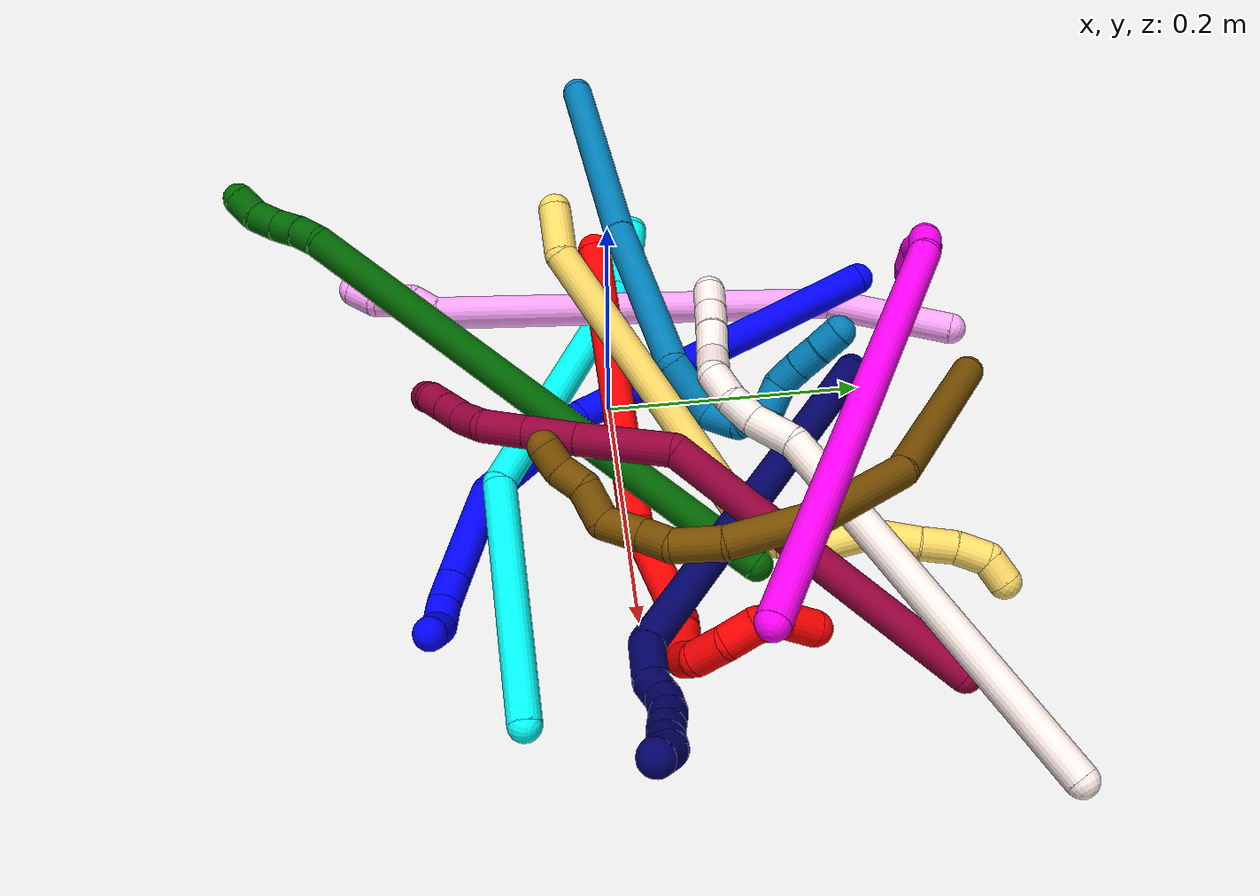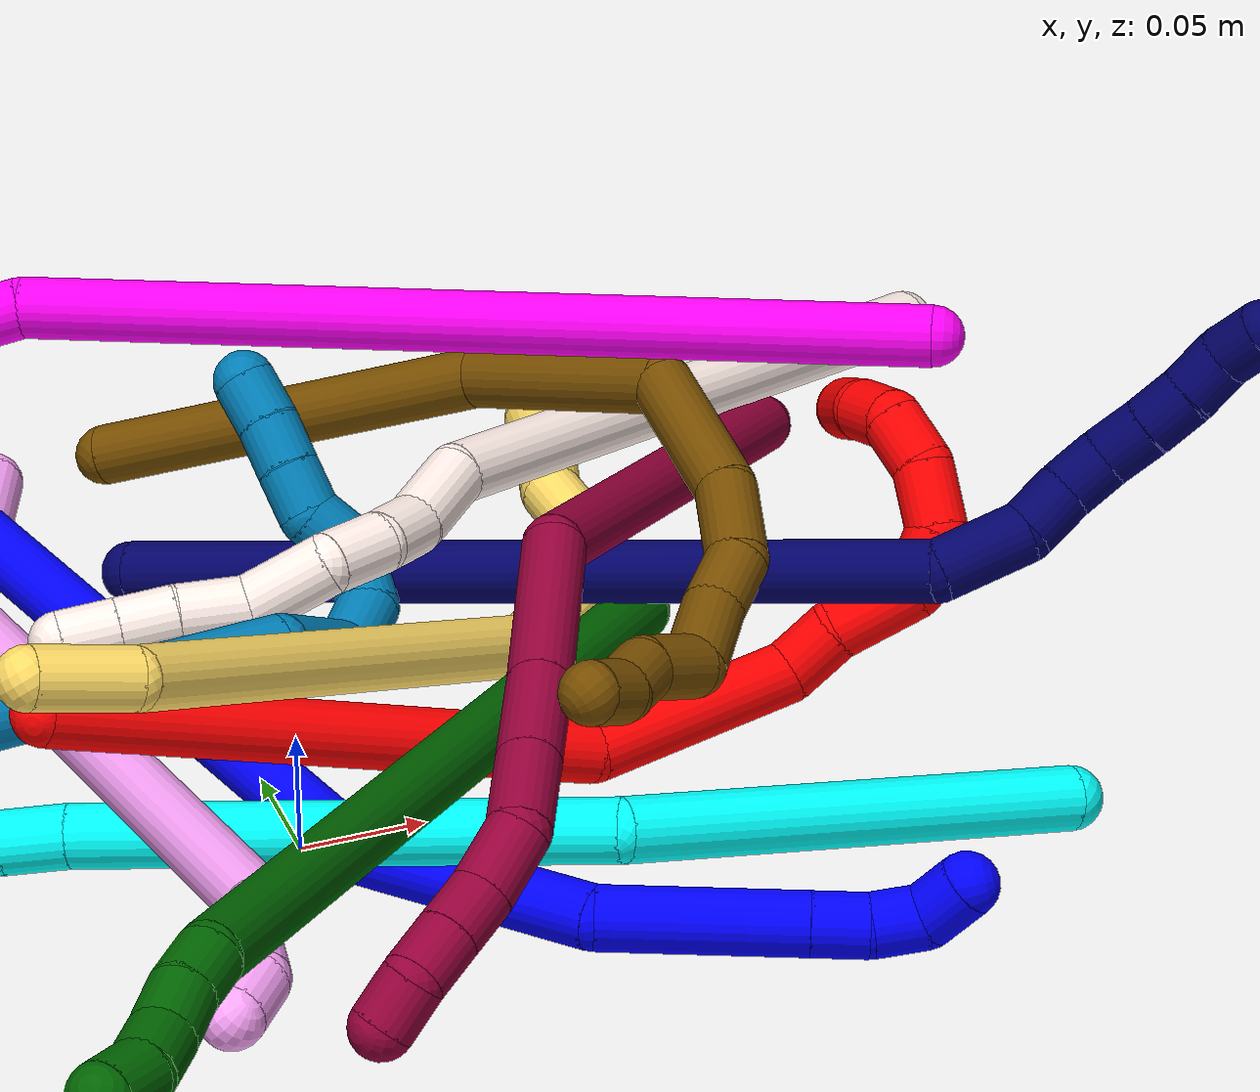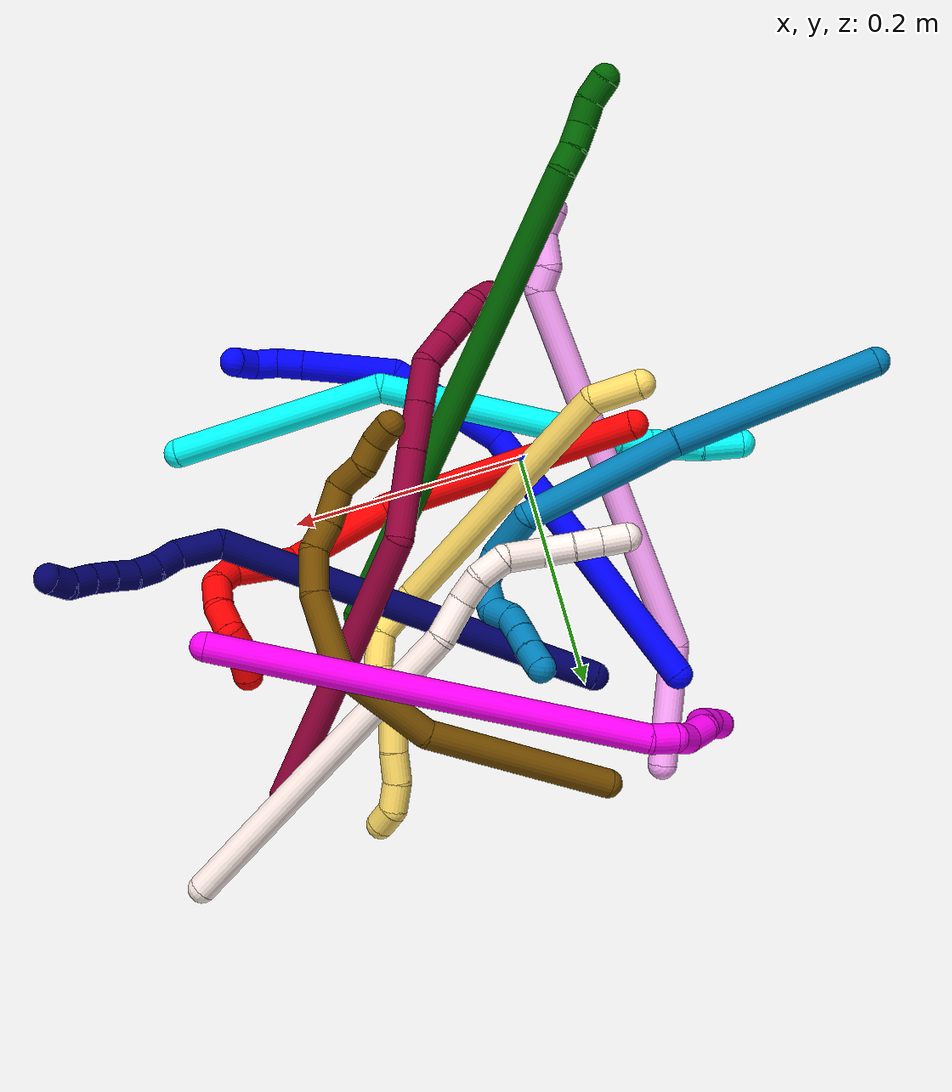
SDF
<sdf version="1.7">
 <world name="default">
  <plugin name="TubeGeneratorPlugin" filename="libtube_generator_plugin.so"/>
  <model name="photoneo_s_sensor">
   <static>1</static>
   <pose>0 0 2 1.57079 1.57079 3.14159</pose>
   <link name="link">
    <inertial><mass>0.1</mass></inertial>
    <sensor name="sensor" type="depth">
     <update_rate>30</update_rate>
     <camera>
      <horizontal_fov>1.22</horizontal_fov>
      <image><width>1920</width><height>1200</height><format>B8G8R8</format></image>
      <clip><near>0.1</near><far>4</far></clip>
      <depth_camera><output>points</output></depth_camera>
     </camera>
     <plugin name="camera_plugin" filename="libgazebo_ros_depth_camera.so">
      <baseline>0.2</baseline>
      <alwaysOn>1</alwaysOn>
      <updateRate>0.0</updateRate>
      <cameraName>camera_ir</cameraName>
      <imageTopicName>/camera/color/image_raw</imageTopicName>
      <cameraInfoTopicName>/camera/color/camera_info</cameraInfoTopicName>
      <depthImageTopicName>/camera/depth/image_raw</depthImageTopicName>
      <depthImageCameraInfoTopicName>/camera/depth/camera_info</depthImageCameraInfoTopicName>
      <pointCloudTopicName>/camera/depth/points</pointCloudTopicName>
      <frameName>fr_optical</frameName>
      <pointCloudCutoff>0.1</pointCloudCutoff>
      <pointCloudCutoffMax>2.0</pointCloudCutoffMax>
      <distortionK1>0</distortionK1>
      <distortionK2>0</distortionK2>
      <distortionK3>0</distortionK3>
      <distortionT1>0</distortionT1>
      <distortionT2>0</distortionT2>
      <CxPrime>0</CxPrime>
      <Cx>0</Cx>
      <Cy>0</Cy>
      <focalLength>0</focalLength>
      <hackBaseline>0</hackBaseline>
     </plugin>
    </sensor>
   </link>
  </model>
  <gravity>0 0 -9.8</gravity>
  <magnetic_field>6e-06 2.3e-05 -4.2e-05</magnetic_field>
  <atmosphere type="adiabatic"/>
  <physics name="default_physics" default="0" type="ode">
   <max_step_size>0.003</max_step_size>
   <real_time_factor>1</real_time_factor>
   <real_time_update_rate>1000</real_time_update_rate>
   <max_contacts>10000</max_contacts>
   <ode>
    <solver>
     <type>quick</type>
     <iters>100</iters>
     <sor>1.3</sor>
     <use_dynamic_moi_rescaling>0</use_dynamic_moi_rescaling>
    </solver>
    <constraints>
     <contact_max_correcting_vel>0</contact_max_correcting_vel>
     <contact_surface_layer>0.001</contact_surface_layer>
     <cfm>0</cfm>
     <erp>0.2</erp>
    </constraints>
   </ode>
  </physics>
  <scene><ambient>0.4 0.4 0.4 1</ambient><background>0.7 0.7 0.7 1</background><shadows>0</shadows></scene>
  <audio><device>default</device></audio>
  <spherical_coordinates>
   <surface_model>EARTH_WGS84</surface_model>
   <latitude_deg>0</latitude_deg>
   <longitude_deg>0</longitude_deg>
   <elevation>0</elevation>
   <heading_deg>0</heading_deg>
  </spherical_coordinates>
  <model name="bin">
   <static>1</static>
   <link name="bottom">
    <collision name="collision-bottom">
     <pose>0 0 -0.01 0 -0 0</pose>
     <geometry><box><size>0.8 0.6 0.02</size></box></geometry>
     <surface>
      <friction><ode><mu>100</mu><mu2>100</mu2></ode></friction>
      <contact><collide_bitmask>65535</collide_bitmask></contact>
     </surface>
    </collision>
   </link>
   <link name="west_wall">
    <collision name="collision-west_wall">
     <pose>-0.41 0 0.1 0 -0 0</pose>
     <geometry><box><size>0.02 0.6 0.2</size></box></geometry>
     <surface>
      <friction><ode><mu>100</mu><mu2>100</mu2></ode></friction>
      <contact><collide_bitmask>65535</collide_bitmask></contact>
     </surface>
    </collision>
   </link>
   <link name="east_wall">
    <collision name="collision-east_wall">
     <pose>0.41 0 0.1 0 -0 0</pose>
     <geometry><box><size>0.02 0.6 0.2</size></box></geometry>
     <surface>
      <friction><ode><mu>100</mu><mu2>100</mu2></ode></friction>
      <contact><collide_bitmask>65535</collide_bitmask></contact>
     </surface>
    </collision>
   </link>
   <link name="south_wall">
    <collision name="collision-south_wall">
     <pose>0 -0.31 0.1 0 -0 0</pose>
     <geometry><box><size>0.8 0.02 0.2</size></box></geometry>
     <surface>
      <friction><ode><mu>100</mu><mu2>100</mu2></ode></friction>
      <contact><collide_bitmask>65535</collide_bitmask></contact>
     </surface>
    </collision>
   </link>
   <link name="north_wall">
    <collision name="collision-north_wall">
     <pose>0 0.31 0.1 0 -0 0</pose>
     <geometry><box><size>0.8 0.02 0.2</size></box></geometry>
     <surface>
      <friction><ode><mu>100</mu><mu2>100</mu2></ode></friction>
      <contact><collide_bitmask>65535</collide_bitmask></contact>
     </surface>
    </collision>
   </link>
  </model>
  <model name="1">
   <static>0</static>
   <link name="1">
    <collision name="collision-cylinder-e_1_1_4">
     <pose>0.076953 -0.066994 0.075211 0.727679 0.652409 0.256225</pose>
     <geometry><cylinder><radius>0.0125</radius><length>0.25351</length></cylinder></geometry>
     <surface>
      <friction><ode><mu>1.16</mu><mu2>1.16</mu2><slip1>0</slip1><slip2>0</slip2></ode></friction>
      <contact><ode><kp>1e+06</kp><kd>1</kd><max_vel>0</max_vel><min_depth>0.001</min_depth></ode></contact>
     </surface>
    </collision>
    <visual name="visual-cylinder-e_1_1_4">
     <pose>0.076953 -0.066994 0.075211 0.727679 0.652409 0.256225</pose>
     <geometry><cylinder><radius>0.0125</radius><length>0.25351</length></cylinder></geometry>
     <material><ambient>0 0 1 1</ambient></material>
    </visual>
    <collision name="collision-cylinder-e_2_4_5">
     <pose>0.173534 -0.152003 0.194668 0.386645 0.389828 0.077259</pose>
     <geometry><cylinder><radius>0.0125</radius><length>0.103294</length></cylinder></geometry>
     <surface>
      <friction><ode><mu>1.16</mu><mu2>1.16</mu2><slip1>0</slip1><slip2>0</slip2></ode></friction>
      <contact><ode><kp>1e+06</kp><kd>1</kd><max_vel>0</max_vel><min_depth>0.001</min_depth></ode></contact>
     </surface>
    </collision>
    <visual name="visual-cylinder-e_2_4_5">
     <pose>0.173534 -0.152003 0.194668 0.386645 0.389828 0.077259</pose>
     <geometry><cylinder><radius>0.0125</radius><length>0.103294</length></cylinder></geometry>
     <material><ambient>0 0 1 1</ambient></material>
    </visual>
    <collision name="collision-cylinder-e_3_5_6">
     <pose>0.201872 -0.167133 0.277561 -0.074485 0.221108 -0.008272</pose>
     <geometry><cylinder><radius>0.0125</radius><length>0.079442</length></cylinder></geometry>
     <surface>
      <friction><ode><mu>1.16</mu><mu2>1.16</mu2><slip1>0</slip1><slip2>0</slip2></ode></friction>
      <contact><ode><kp>1e+06</kp><kd>1</kd><max_vel>0</max_vel><min_depth>0.001</min_depth></ode></contact>
     </surface>
    </collision>
    <visual name="visual-cylinder-e_3_5_6">
     <pose>0.201872 -0.167133 0.277561 -0.074485 0.221108 -0.008272</pose>
     <geometry><cylinder><radius>0.0125</radius><length>0.079442</length></cylinder></geometry>
     <material><ambient>0 0 1 1</ambient></material>
    </visual>
    <collision name="collision-cylinder-e_4_6_7">
     <pose>0.213014 -0.163363 0.326887 -0.082745 0.223052 -0.009272</pose>
     <geometry><cylinder><radius>0.0125</radius><length>0.021976</length></cylinder></geometry>
     <surface>
      <friction><ode><mu>1.16</mu><mu2>1.16</mu2><slip1>0</slip1><slip2>0</slip2></ode></friction>
      <contact><ode><kp>1e+06</kp><kd>1</kd><max_vel>0</max_vel><min_depth>0.001</min_depth></ode></contact>
     </surface>
    </collision>
    <visual name="visual-cylinder-e_4_6_7">
     <pose>0.213014 -0.163363 0.326887 -0.082745 0.223052 -0.009272</pose>
     <geometry><cylinder><radius>0.0125</radius><length>0.021976</length></cylinder></geometry>
     <material><ambient>0 0 1 1</ambient></material>
    </visual>
    <collision name="collision-cylinder-e_5_7_8">
     <pose>0.215849 -0.160691 0.347771 -0.173312 0.039024 -0.003391</pose>
     <geometry><cylinder><radius>0.0125</radius><length>0.020736</length></cylinder></geometry>
     <surface>
      <friction><ode><mu>1.16</mu><mu2>1.16</mu2><slip1>0</slip1><slip2>0</slip2></ode></friction>
      <contact><ode><kp>1e+06</kp><kd>1</kd><max_vel>0</max_vel><min_depth>0.001</min_depth></ode></contact>
     </surface>
    </collision>
    <visual name="visual-cylinder-e_5_7_8">
     <pose>0.215849 -0.160691 0.347771 -0.173312 0.039024 -0.003391</pose>
     <geometry><cylinder><radius>0.0125</radius><length>0.020736</length></cylinder></geometry>
     <material><ambient>0 0 1 1</ambient></material>
    </visual>
    <collision name="collision-cylinder-e_6_8_2">
     <pose>0.211552 -0.162159 0.366807 0.353047 -0.463353 -0.084115</pose>
     <geometry><cylinder><radius>0.0125</radius><length>0.021042</length></cylinder></geometry>
     <surface>
      <friction><ode><mu>1.16</mu><mu2>1.16</mu2><slip1>0</slip1><slip2>0</slip2></ode></friction>
      <contact><ode><kp>1e+06</kp><kd>1</kd><max_vel>0</max_vel><min_depth>0.001</min_depth></ode></contact>
     </surface>
    </collision>
    <visual name="visual-cylinder-e_6_8_2">
     <pose>0.211552 -0.162159 0.366807 0.353047 -0.463353 -0.084115</pose>
     <geometry><cylinder><radius>0.0125</radius><length>0.021042</length></cylinder></geometry>
     <material><ambient>0 0 1 1</ambient></material>
    </visual>
    <collision name="collision-sphere-2">
     <pose>0.206849 -0.165413 0.375638 0 -0 0</pose>
     <geometry><sphere><radius>0.0125</radius></sphere></geometry>
     <surface>
      <friction><ode><mu>1.16</mu><mu2>1.16</mu2><slip1>0</slip1><slip2>0</slip2></ode></friction>
      <contact><ode><kp>1e+06</kp><kd>1</kd><max_vel>0</max_vel><min_depth>0.001</min_depth></ode></contact>
     </surface>
    </collision>
    <visual name="visual-sphere-2">
     <pose>0.206849 -0.165413 0.375638 0 -0 0</pose>
     <geometry><sphere><radius>0.0125</radius></sphere></geometry>
     <material><ambient>0 0 1 1</ambient></material>
    </visual>
    <collision name="collision-sphere-4">
     <pose>0.153906 -0.133989 0.150423 0 -0 0</pose>
     <geometry><sphere><radius>0.0125</radius></sphere></geometry>
     <surface>
      <friction><ode><mu>1.16</mu><mu2>1.16</mu2><slip1>0</slip1><slip2>0</slip2></ode></friction>
      <contact><ode><kp>1e+06</kp><kd>1</kd><max_vel>0</max_vel><min_depth>0.001</min_depth></ode></contact>
     </surface>
    </collision>
    <visual name="visual-sphere-4">
     <pose>0.153906 -0.133989 0.150423 0 -0 0</pose>
     <geometry><sphere><radius>0.0125</radius></sphere></geometry>
     <material><ambient>0 0 1 1</ambient></material>
    </visual>
    <collision name="collision-sphere-1">
     <geometry><sphere><radius>0.0125</radius></sphere></geometry>
     <surface>
      <friction><ode><mu>1.16</mu><mu2>1.16</mu2><slip1>0</slip1><slip2>0</slip2></ode></friction>
      <contact><ode><kp>1e+06</kp><kd>1</kd><max_vel>0</max_vel><min_depth>0.001</min_depth></ode></contact>
     </surface>
    </collision>
    <visual name="visual-sphere-1">
     <geometry><sphere><radius>0.0125</radius></sphere></geometry>
     <material><ambient>0 0 1 1</ambient></material>
    </visual>
    <collision name="collision-sphere-8">
     <pose>0.216254 -0.158905 0.357975 0 -0 0</pose>
     <geometry><sphere><radius>0.0125</radius></sphere></geometry>
     <surface>
      <friction><ode><mu>1.16</mu><mu2>1.16</mu2><slip1>0</slip1><slip2>0</slip2></ode></friction>
      <contact><ode><kp>1e+06</kp><kd>1</kd><max_vel>0</max_vel><min_depth>0.001</min_depth></ode></contact>
     </surface>
    </collision>
    <visual name="visual-sphere-8">
     <pose>0.216254 -0.158905 0.357975 0 -0 0</pose>
     <geometry><sphere><radius>0.0125</radius></sphere></geometry>
     <material><ambient>0 0 1 1</ambient></material>
    </visual>
    <collision name="collision-sphere-5">
     <pose>0.193161 -0.170017 0.238914 0 -0 0</pose>
     <geometry><sphere><radius>0.0125</radius></sphere></geometry>
     <surface>
      <friction><ode><mu>1.16</mu><mu2>1.16</mu2><slip1>0</slip1><slip2>0</slip2></ode></friction>
      <contact><ode><kp>1e+06</kp><kd>1</kd><max_vel>0</max_vel><min_depth>0.001</min_depth></ode></contact>
     </surface>
    </collision>
    <visual name="visual-sphere-5">
     <pose>0.193161 -0.170017 0.238914 0 -0 0</pose>
     <geometry><sphere><radius>0.0125</radius></sphere></geometry>
     <material><ambient>0 0 1 1</ambient></material>
    </visual>
    <collision name="collision-sphere-6">
     <pose>0.210584 -0.164249 0.316207 0 -0 0</pose>
     <geometry><sphere><radius>0.0125</radius></sphere></geometry>
     <surface>
      <friction><ode><mu>1.16</mu><mu2>1.16</mu2><slip1>0</slip1><slip2>0</slip2></ode></friction>
      <contact><ode><kp>1e+06</kp><kd>1</kd><max_vel>0</max_vel><min_depth>0.001</min_depth></ode></contact>
     </surface>
    </collision>
    <visual name="visual-sphere-6">
     <pose>0.210584 -0.164249 0.316207 0 -0 0</pose>
     <geometry><sphere><radius>0.0125</radius></sphere></geometry>
     <material><ambient>0 0 1 1</ambient></material>
    </visual>
    <collision name="collision-sphere-7">
     <pose>0.215445 -0.162478 0.337566 0 -0 0</pose>
     <geometry><sphere><radius>0.0125</radius></sphere></geometry>
     <surface>
      <friction><ode><mu>1.16</mu><mu2>1.16</mu2><slip1>0</slip1><slip2>0</slip2></ode></friction>
      <contact><ode><kp>1e+06</kp><kd>1</kd><max_vel>0</max_vel><min_depth>0.001</min_depth></ode></contact>
     </surface>
    </collision>
    <visual name="visual-sphere-7">
     <pose>0.215445 -0.162478 0.337566 0 -0 0</pose>
     <geometry><sphere><radius>0.0125</radius></sphere></geometry>
     <material><ambient>0 0 1 1</ambient></material>
    </visual>
    <inertial>
     <pose>0.134158 -0.112593 0.166677 0 -0 0</pose>
     <mass>0.5</mass>
     <inertia>
      <ixx>0.001486</ixx>
      <ixy>0</ixy>
      <ixz>0</ixz>
      <iyy>0.001536</iyy>
      <iyz>0</iyz>
      <izz>-9.4e-05</izz>
     </inertia>
    </inertial>
   </link>
   <pose>-0.07611 0.211367 0.045623 -1.17382 1.01192 -1.56068</pose>
  </model>
  <model name="2">
   <static>0</static>
   <link name="2">
    <collision name="collision-cylinder-e_1_1_4">
     <pose>0.079398 -0.046987 -0.067601 2.53419 0.767291 1.8212</pose>
     <geometry><cylinder><radius>0.0125</radius><length>0.228752</length></cylinder></geometry>
     <surface>
      <friction><ode><mu>1.16</mu><mu2>1.16</mu2><slip1>0</slip1><slip2>0</slip2></ode></friction>
      <contact><ode><kp>1e+06</kp><kd>1</kd><max_vel>0</max_vel><min_depth>0.001</min_depth></ode></contact>
     </surface>
    </collision>
    <visual name="visual-cylinder-e_1_1_4">
     <pose>0.079398 -0.046987 -0.067601 2.53419 0.767291 1.8212</pose>
     <geometry><cylinder><radius>0.0125</radius><length>0.228752</length></cylinder></geometry>
     <material><ambient>1 0 0 1</ambient></material>
    </visual>
    <collision name="collision-cylinder-e_2_4_5">
     <pose>0.191431 -0.095195 -0.167931 3.10433 0.783607 3.05147</pose>
     <geometry><cylinder><radius>0.0125</radius><length>0.092468</length></cylinder></geometry>
     <surface>
      <friction><ode><mu>1.16</mu><mu2>1.16</mu2><slip1>0</slip1><slip2>0</slip2></ode></friction>
      <contact><ode><kp>1e+06</kp><kd>1</kd><max_vel>0</max_vel><min_depth>0.001</min_depth></ode></contact>
     </surface>
    </collision>
    <visual name="visual-cylinder-e_2_4_5">
     <pose>0.191431 -0.095195 -0.167931 3.10433 0.783607 3.05147</pose>
     <geometry><cylinder><radius>0.0125</radius><length>0.092468</length></cylinder></geometry>
     <material><ambient>1 0 0 1</ambient></material>
    </visual>
    <collision name="collision-cylinder-e_3_5_6">
     <pose>0.234693 -0.08995 -0.20332 -1.96134 0.989018 -1.35566</pose>
     <geometry><cylinder><radius>0.0125</radius><length>0.025442</length></cylinder></geometry>
     <surface>
      <friction><ode><mu>1.16</mu><mu2>1.16</mu2><slip1>0</slip1><slip2>0</slip2></ode></friction>
      <contact><ode><kp>1e+06</kp><kd>1</kd><max_vel>0</max_vel><min_depth>0.001</min_depth></ode></contact>
     </surface>
    </collision>
    <visual name="visual-cylinder-e_3_5_6">
     <pose>0.234693 -0.08995 -0.20332 -1.96134 0.989018 -1.35566</pose>
     <geometry><cylinder><radius>0.0125</radius><length>0.025442</length></cylinder></geometry>
     <material><ambient>1 0 0 1</ambient></material>
    </visual>
    <collision name="collision-cylinder-e_4_6_7">
     <pose>0.261578 -0.079057 -0.211367 -2.45329 1.16561 -2.14557</pose>
     <geometry><cylinder><radius>0.0125</radius><length>0.035378</length></cylinder></geometry>
     <surface>
      <friction><ode><mu>1.16</mu><mu2>1.16</mu2><slip1>0</slip1><slip2>0</slip2></ode></friction>
      <contact><ode><kp>1e+06</kp><kd>1</kd><max_vel>0</max_vel><min_depth>0.001</min_depth></ode></contact>
     </surface>
    </collision>
    <visual name="visual-cylinder-e_4_6_7">
     <pose>0.261578 -0.079057 -0.211367 -2.45329 1.16561 -2.14557</pose>
     <geometry><cylinder><radius>0.0125</radius><length>0.035378</length></cylinder></geometry>
     <material><ambient>1 0 0 1</ambient></material>
    </visual>
    <collision name="collision-cylinder-e_5_7_8">
     <pose>0.283726 -0.065082 -0.220939 -1.98417 0.514417 -0.765504</pose>
     <geometry><cylinder><radius>0.0125</radius><length>0.023946</length></cylinder></geometry>
     <surface>
      <friction><ode><mu>1.16</mu><mu2>1.16</mu2><slip1>0</slip1><slip2>0</slip2></ode></friction>
      <contact><ode><kp>1e+06</kp><kd>1</kd><max_vel>0</max_vel><min_depth>0.001</min_depth></ode></contact>
     </surface>
    </collision>
    <visual name="visual-cylinder-e_5_7_8">
     <pose>0.283726 -0.065082 -0.220939 -1.98417 0.514417 -0.765504</pose>
     <geometry><cylinder><radius>0.0125</radius><length>0.023946</length></cylinder></geometry>
     <material><ambient>1 0 0 1</ambient></material>
    </visual>
    <collision name="collision-cylinder-e_6_8_9">
     <pose>0.288033 -0.0441 -0.231753 -2.09594 -0.119243 0.206412</pose>
     <geometry><cylinder><radius>0.0125</radius><length>0.026625</length></cylinder></geometry>
     <surface>
      <friction><ode><mu>1.16</mu><mu2>1.16</mu2><slip1>0</slip1><slip2>0</slip2></ode></friction>
      <contact><ode><kp>1e+06</kp><kd>1</kd><max_vel>0</max_vel><min_depth>0.001</min_depth></ode></contact>
     </surface>
    </collision>
    <visual name="visual-cylinder-e_6_8_9">
     <pose>0.288033 -0.0441 -0.231753 -2.09594 -0.119243 0.206412</pose>
     <geometry><cylinder><radius>0.0125</radius><length>0.026625</length></cylinder></geometry>
     <material><ambient>1 0 0 1</ambient></material>
    </visual>
    <collision name="collision-cylinder-e_7_9_10">
     <pose>0.280923 -0.024314 -0.244627 -2.21319 -0.487305 0.921685</pose>
     <geometry><cylinder><radius>0.0125</radius><length>0.023604</length></cylinder></geometry>
     <surface>
      <friction><ode><mu>1.16</mu><mu2>1.16</mu2><slip1>0</slip1><slip2>0</slip2></ode></friction>
      <contact><ode><kp>1e+06</kp><kd>1</kd><max_vel>0</max_vel><min_depth>0.001</min_depth></ode></contact>
     </surface>
    </collision>
    <visual name="visual-cylinder-e_7_9_10">
     <pose>0.280923 -0.024314 -0.244627 -2.21319 -0.487305 0.921685</pose>
     <geometry><cylinder><radius>0.0125</radius><length>0.023604</length></cylinder></geometry>
     <material><ambient>1 0 0 1</ambient></material>
    </visual>
    <collision name="collision-cylinder-e_8_10_11">
     <pose>0.268152 -0.015262 -0.258447 -3.04916 -0.761187 2.91143</pose>
     <geometry><cylinder><radius>0.0125</radius><length>0.021005</length></cylinder></geometry>
     <surface>
      <friction><ode><mu>1.16</mu><mu2>1.16</mu2><slip1>0</slip1><slip2>0</slip2></ode></friction>
      <contact><ode><kp>1e+06</kp><kd>1</kd><max_vel>0</max_vel><min_depth>0.001</min_depth></ode></contact>
     </surface>
    </collision>
    <visual name="visual-cylinder-e_8_10_11">
     <pose>0.268152 -0.015262 -0.258447 -3.04916 -0.761187 2.91143</pose>
     <geometry><cylinder><radius>0.0125</radius><length>0.021005</length></cylinder></geometry>
     <material><ambient>1 0 0 1</ambient></material>
    </visual>
    <collision name="collision-cylinder-e_9_11_2">
     <pose>0.255418 -0.016833 -0.275735 2.91185 -0.502929 -2.29734</pose>
     <geometry><cylinder><radius>0.0125</radius><length>0.022779</length></cylinder></geometry>
     <surface>
      <friction><ode><mu>1.16</mu><mu2>1.16</mu2><slip1>0</slip1><slip2>0</slip2></ode></friction>
      <contact><ode><kp>1e+06</kp><kd>1</kd><max_vel>0</max_vel><min_depth>0.001</min_depth></ode></contact>
     </surface>
    </collision>
    <visual name="visual-cylinder-e_9_11_2">
     <pose>0.255418 -0.016833 -0.275735 2.91185 -0.502929 -2.29734</pose>
     <geometry><cylinder><radius>0.0125</radius><length>0.022779</length></cylinder></geometry>
     <material><ambient>1 0 0 1</ambient></material>
    </visual>
    <collision name="collision-sphere-2">
     <pose>0.249928 -0.019106 -0.285452 0 -0 0</pose>
     <geometry><sphere><radius>0.0125</radius></sphere></geometry>
     <surface>
      <friction><ode><mu>1.16</mu><mu2>1.16</mu2><slip1>0</slip1><slip2>0</slip2></ode></friction>
      <contact><ode><kp>1e+06</kp><kd>1</kd><max_vel>0</max_vel><min_depth>0.001</min_depth></ode></contact>
     </surface>
    </collision>
    <visual name="visual-sphere-2">
     <pose>0.249928 -0.019106 -0.285452 0 -0 0</pose>
     <geometry><sphere><radius>0.0125</radius></sphere></geometry>
     <material><ambient>1 0 0 1</ambient></material>
    </visual>
    <collision name="collision-sphere-11">
     <pose>0.260908 -0.01456 -0.266018 0 -0 0</pose>
     <geometry><sphere><radius>0.0125</radius></sphere></geometry>
     <surface>
      <friction><ode><mu>1.16</mu><mu2>1.16</mu2><slip1>0</slip1><slip2>0</slip2></ode></friction>
      <contact><ode><kp>1e+06</kp><kd>1</kd><max_vel>0</max_vel><min_depth>0.001</min_depth></ode></contact>
     </surface>
    </collision>
    <visual name="visual-sphere-11">
     <pose>0.260908 -0.01456 -0.266018 0 -0 0</pose>
     <geometry><sphere><radius>0.0125</radius></sphere></geometry>
     <material><ambient>1 0 0 1</ambient></material>
    </visual>
    <collision name="collision-sphere-10">
     <pose>0.275397 -0.015964 -0.250875 0 -0 0</pose>
     <geometry><sphere><radius>0.0125</radius></sphere></geometry>
     <surface>
      <friction><ode><mu>1.16</mu><mu2>1.16</mu2><slip1>0</slip1><slip2>0</slip2></ode></friction>
      <contact><ode><kp>1e+06</kp><kd>1</kd><max_vel>0</max_vel><min_depth>0.001</min_depth></ode></contact>
     </surface>
    </collision>
    <visual name="visual-sphere-10">
     <pose>0.275397 -0.015964 -0.250875 0 -0 0</pose>
     <geometry><sphere><radius>0.0125</radius></sphere></geometry>
     <material><ambient>1 0 0 1</ambient></material>
    </visual>
    <collision name="collision-sphere-9">
     <pose>0.286449 -0.032663 -0.23838 0 -0 0</pose>
     <geometry><sphere><radius>0.0125</radius></sphere></geometry>
     <surface>
      <friction><ode><mu>1.16</mu><mu2>1.16</mu2><slip1>0</slip1><slip2>0</slip2></ode></friction>
      <contact><ode><kp>1e+06</kp><kd>1</kd><max_vel>0</max_vel><min_depth>0.001</min_depth></ode></contact>
     </surface>
    </collision>
    <visual name="visual-sphere-9">
     <pose>0.286449 -0.032663 -0.23838 0 -0 0</pose>
     <geometry><sphere><radius>0.0125</radius></sphere></geometry>
     <material><ambient>1 0 0 1</ambient></material>
    </visual>
    <collision name="collision-sphere-4">
     <pose>0.158797 -0.093975 -0.135203 0 -0 0</pose>
     <geometry><sphere><radius>0.0125</radius></sphere></geometry>
     <surface>
      <friction><ode><mu>1.16</mu><mu2>1.16</mu2><slip1>0</slip1><slip2>0</slip2></ode></friction>
      <contact><ode><kp>1e+06</kp><kd>1</kd><max_vel>0</max_vel><min_depth>0.001</min_depth></ode></contact>
     </surface>
    </collision>
    <visual name="visual-sphere-4">
     <pose>0.158797 -0.093975 -0.135203 0 -0 0</pose>
     <geometry><sphere><radius>0.0125</radius></sphere></geometry>
     <material><ambient>1 0 0 1</ambient></material>
    </visual>
    <collision name="collision-sphere-1">
     <geometry><sphere><radius>0.0125</radius></sphere></geometry>
     <surface>
      <friction><ode><mu>1.16</mu><mu2>1.16</mu2><slip1>0</slip1><slip2>0</slip2></ode></friction>
      <contact><ode><kp>1e+06</kp><kd>1</kd><max_vel>0</max_vel><min_depth>0.001</min_depth></ode></contact>
     </surface>
    </collision>
    <visual name="visual-sphere-1">
     <geometry><sphere><radius>0.0125</radius></sphere></geometry>
     <material><ambient>1 0 0 1</ambient></material>
    </visual>
    <collision name="collision-sphere-8">
     <pose>0.289617 -0.055537 -0.225126 0 -0 0</pose>
     <geometry><sphere><radius>0.0125</radius></sphere></geometry>
     <surface>
      <friction><ode><mu>1.16</mu><mu2>1.16</mu2><slip1>0</slip1><slip2>0</slip2></ode></friction>
      <contact><ode><kp>1e+06</kp><kd>1</kd><max_vel>0</max_vel><min_depth>0.001</min_depth></ode></contact>
     </surface>
    </collision>
    <visual name="visual-sphere-8">
     <pose>0.289617 -0.055537 -0.225126 0 -0 0</pose>
     <geometry><sphere><radius>0.0125</radius></sphere></geometry>
     <material><ambient>1 0 0 1</ambient></material>
    </visual>
    <collision name="collision-sphere-5">
     <pose>0.224065 -0.096415 -0.200659 0 -0 0</pose>
     <geometry><sphere><radius>0.0125</radius></sphere></geometry>
     <surface>
      <friction><ode><mu>1.16</mu><mu2>1.16</mu2><slip1>0</slip1><slip2>0</slip2></ode></friction>
      <contact><ode><kp>1e+06</kp><kd>1</kd><max_vel>0</max_vel><min_depth>0.001</min_depth></ode></contact>
     </surface>
    </collision>
    <visual name="visual-sphere-5">
     <pose>0.224065 -0.096415 -0.200659 0 -0 0</pose>
     <geometry><sphere><radius>0.0125</radius></sphere></geometry>
     <material><ambient>1 0 0 1</ambient></material>
    </visual>
    <collision name="collision-sphere-6">
     <pose>0.245322 -0.083486 -0.205982 0 -0 0</pose>
     <geometry><sphere><radius>0.0125</radius></sphere></geometry>
     <surface>
      <friction><ode><mu>1.16</mu><mu2>1.16</mu2><slip1>0</slip1><slip2>0</slip2></ode></friction>
      <contact><ode><kp>1e+06</kp><kd>1</kd><max_vel>0</max_vel><min_depth>0.001</min_depth></ode></contact>
     </surface>
    </collision>
    <visual name="visual-sphere-6">
     <pose>0.245322 -0.083486 -0.205982 0 -0 0</pose>
     <geometry><sphere><radius>0.0125</radius></sphere></geometry>
     <material><ambient>1 0 0 1</ambient></material>
    </visual>
    <collision name="collision-sphere-7">
     <pose>0.277835 -0.074628 -0.216752 0 -0 0</pose>
     <geometry><sphere><radius>0.0125</radius></sphere></geometry>
     <surface>
      <friction><ode><mu>1.16</mu><mu2>1.16</mu2><slip1>0</slip1><slip2>0</slip2></ode></friction>
      <contact><ode><kp>1e+06</kp><kd>1</kd><max_vel>0</max_vel><min_depth>0.001</min_depth></ode></contact>
     </surface>
    </collision>
    <visual name="visual-sphere-7">
     <pose>0.277835 -0.074628 -0.216752 0 -0 0</pose>
     <geometry><sphere><radius>0.0125</radius></sphere></geometry>
     <material><ambient>1 0 0 1</ambient></material>
    </visual>
    <inertial>
     <pose>0.167267 -0.057294 -0.145176 0 -0 0</pose>
     <mass>0.5</mass>
     <inertia>
      <ixx>0.000496</ixx>
      <ixy>0</ixy>
      <ixz>0</ixz>
      <iyy>0.00137</iyy>
      <iyz>0</iyz>
      <izz>-0.000367</izz>
     </inertia>
    </inertial>
   </link>
   <pose>-0.096255 -0.000779 0.083128 1.39017 -0.26187 -0.526142</pose>
  </model>
  <model name="3">
   <static>0</static>
   <link name="3">
    <collision name="collision-cylinder-e_1_1_4">
     <pose>-0.077036 -0.004174 -0.0517 3.06103 -0.978219 -2.99044</pose>
     <geometry><cylinder><radius>0.0125</radius><length>0.185739</length></cylinder></geometry>
     <surface>
      <friction><ode><mu>1.16</mu><mu2>1.16</mu2><slip1>0</slip1><slip2>0</slip2></ode></friction>
      <contact><ode><kp>1e+06</kp><kd>1</kd><max_vel>0</max_vel><min_depth>0.001</min_depth></ode></contact>
     </surface>
    </collision>
    <visual name="visual-cylinder-e_1_1_4">
     <pose>-0.077036 -0.004174 -0.0517 3.06103 -0.978219 -2.99044</pose>
     <geometry><cylinder><radius>0.0125</radius><length>0.185739</length></cylinder></geometry>
     <material><ambient>0.003922 1 0.996078 1</ambient></material>
    </visual>
    <collision name="collision-cylinder-e_2_4_5">
     <pose>-0.249142 0.031866 -0.122276 -2.00967 -1.13367 1.57273</pose>
     <geometry><cylinder><radius>0.0125</radius><length>0.209874</length></cylinder></geometry>
     <surface>
      <friction><ode><mu>1.16</mu><mu2>1.16</mu2><slip1>0</slip1><slip2>0</slip2></ode></friction>
      <contact><ode><kp>1e+06</kp><kd>1</kd><max_vel>0</max_vel><min_depth>0.001</min_depth></ode></contact>
     </surface>
    </collision>
    <visual name="visual-cylinder-e_2_4_5">
     <pose>-0.249142 0.031866 -0.122276 -2.00967 -1.13367 1.57273</pose>
     <geometry><cylinder><radius>0.0125</radius><length>0.209874</length></cylinder></geometry>
     <material><ambient>0.003922 1 0.996078 1</ambient></material>
    </visual>
    <collision name="collision-cylinder-e_3_5_6">
     <pose>-0.355518 0.076736 -0.14504 -2.26651 -1.07832 1.81443</pose>
     <geometry><cylinder><radius>0.0125</radius><length>0.025661</length></cylinder></geometry>
     <surface>
      <friction><ode><mu>1.16</mu><mu2>1.16</mu2><slip1>0</slip1><slip2>0</slip2></ode></friction>
      <contact><ode><kp>1e+06</kp><kd>1</kd><max_vel>0</max_vel><min_depth>0.001</min_depth></ode></contact>
     </surface>
    </collision>
    <visual name="visual-cylinder-e_3_5_6">
     <pose>-0.355518 0.076736 -0.14504 -2.26651 -1.07832 1.81443</pose>
     <geometry><cylinder><radius>0.0125</radius><length>0.025661</length></cylinder></geometry>
     <material><ambient>0.003922 1 0.996078 1</ambient></material>
    </visual>
    <collision name="collision-cylinder-e_4_6_7">
     <pose>-0.386913 0.088047 -0.156099 -2.39353 -1.11766 2.02054</pose>
     <geometry><cylinder><radius>0.0125</radius><length>0.04469</length></cylinder></geometry>
     <surface>
      <friction><ode><mu>1.16</mu><mu2>1.16</mu2><slip1>0</slip1><slip2>0</slip2></ode></friction>
      <contact><ode><kp>1e+06</kp><kd>1</kd><max_vel>0</max_vel><min_depth>0.001</min_depth></ode></contact>
     </surface>
    </collision>
    <visual name="visual-cylinder-e_4_6_7">
     <pose>-0.386913 0.088047 -0.156099 -2.39353 -1.11766 2.02054</pose>
     <geometry><cylinder><radius>0.0125</radius><length>0.04469</length></cylinder></geometry>
     <material><ambient>0.003922 1 0.996078 1</ambient></material>
    </visual>
    <collision name="collision-cylinder-e_5_7_2">
     <pose>-0.421452 0.099313 -0.170988 -2.60299 -1.01411 2.21932</pose>
     <geometry><cylinder><radius>0.0125</radius><length>0.034035</length></cylinder></geometry>
     <surface>
      <friction><ode><mu>1.16</mu><mu2>1.16</mu2><slip1>0</slip1><slip2>0</slip2></ode></friction>
      <contact><ode><kp>1e+06</kp><kd>1</kd><max_vel>0</max_vel><min_depth>0.001</min_depth></ode></contact>
     </surface>
    </collision>
    <visual name="visual-cylinder-e_5_7_2">
     <pose>-0.421452 0.099313 -0.170988 -2.60299 -1.01411 2.21932</pose>
     <geometry><cylinder><radius>0.0125</radius><length>0.034035</length></cylinder></geometry>
     <material><ambient>0.003922 1 0.996078 1</ambient></material>
    </visual>
    <collision name="collision-sphere-2">
     <pose>-0.4359 0.103925 -0.178707 0 -0 0</pose>
     <geometry><sphere><radius>0.0125</radius></sphere></geometry>
     <surface>
      <friction><ode><mu>1.16</mu><mu2>1.16</mu2><slip1>0</slip1><slip2>0</slip2></ode></friction>
      <contact><ode><kp>1e+06</kp><kd>1</kd><max_vel>0</max_vel><min_depth>0.001</min_depth></ode></contact>
     </surface>
    </collision>
    <visual name="visual-sphere-2">
     <pose>-0.4359 0.103925 -0.178707 0 -0 0</pose>
     <geometry><sphere><radius>0.0125</radius></sphere></geometry>
     <material><ambient>0.003922 1 0.996078 1</ambient></material>
    </visual>
    <collision name="collision-sphere-7">
     <pose>-0.407003 0.094701 -0.163269 0 -0 0</pose>
     <geometry><sphere><radius>0.0125</radius></sphere></geometry>
     <surface>
      <friction><ode><mu>1.16</mu><mu2>1.16</mu2><slip1>0</slip1><slip2>0</slip2></ode></friction>
      <contact><ode><kp>1e+06</kp><kd>1</kd><max_vel>0</max_vel><min_depth>0.001</min_depth></ode></contact>
     </surface>
    </collision>
    <visual name="visual-sphere-7">
     <pose>-0.407003 0.094701 -0.163269 0 -0 0</pose>
     <geometry><sphere><radius>0.0125</radius></sphere></geometry>
     <material><ambient>0.003922 1 0.996078 1</ambient></material>
    </visual>
    <collision name="collision-sphere-6">
     <pose>-0.366824 0.081393 -0.148928 0 -0 0</pose>
     <geometry><sphere><radius>0.0125</radius></sphere></geometry>
     <surface>
      <friction><ode><mu>1.16</mu><mu2>1.16</mu2><slip1>0</slip1><slip2>0</slip2></ode></friction>
      <contact><ode><kp>1e+06</kp><kd>1</kd><max_vel>0</max_vel><min_depth>0.001</min_depth></ode></contact>
     </surface>
    </collision>
    <visual name="visual-sphere-6">
     <pose>-0.366824 0.081393 -0.148928 0 -0 0</pose>
     <geometry><sphere><radius>0.0125</radius></sphere></geometry>
     <material><ambient>0.003922 1 0.996078 1</ambient></material>
    </visual>
    <collision name="collision-sphere-5">
     <pose>-0.344212 0.072079 -0.141152 0 -0 0</pose>
     <geometry><sphere><radius>0.0125</radius></sphere></geometry>
     <surface>
      <friction><ode><mu>1.16</mu><mu2>1.16</mu2><slip1>0</slip1><slip2>0</slip2></ode></friction>
      <contact><ode><kp>1e+06</kp><kd>1</kd><max_vel>0</max_vel><min_depth>0.001</min_depth></ode></contact>
     </surface>
    </collision>
    <visual name="visual-sphere-5">
     <pose>-0.344212 0.072079 -0.141152 0 -0 0</pose>
     <geometry><sphere><radius>0.0125</radius></sphere></geometry>
     <material><ambient>0.003922 1 0.996078 1</ambient></material>
    </visual>
    <collision name="collision-sphere-1">
     <geometry><sphere><radius>0.0125</radius></sphere></geometry>
     <surface>
      <friction><ode><mu>1.16</mu><mu2>1.16</mu2><slip1>0</slip1><slip2>0</slip2></ode></friction>
      <contact><ode><kp>1e+06</kp><kd>1</kd><max_vel>0</max_vel><min_depth>0.001</min_depth></ode></contact>
     </surface>
    </collision>
    <visual name="visual-sphere-1">
     <geometry><sphere><radius>0.0125</radius></sphere></geometry>
     <material><ambient>0.003922 1 0.996078 1</ambient></material>
    </visual>
    <collision name="collision-sphere-4">
     <pose>-0.154071 -0.008348 -0.103399 0 -0 0</pose>
     <geometry><sphere><radius>0.0125</radius></sphere></geometry>
     <surface>
      <friction><ode><mu>1.16</mu><mu2>1.16</mu2><slip1>0</slip1><slip2>0</slip2></ode></friction>
      <contact><ode><kp>1e+06</kp><kd>1</kd><max_vel>0</max_vel><min_depth>0.001</min_depth></ode></contact>
     </surface>
    </collision>
    <visual name="visual-sphere-4">
     <pose>-0.154071 -0.008348 -0.103399 0 -0 0</pose>
     <geometry><sphere><radius>0.0125</radius></sphere></geometry>
     <material><ambient>0.003922 1 0.996078 1</ambient></material>
    </visual>
    <inertial>
     <pose>-0.214711 0.030393 -0.103565 0 -0 0</pose>
     <mass>0.5</mass>
     <inertia>
      <ixx>-4.6e-05</ixx>
      <ixy>0</ixy>
      <ixz>0</ixz>
      <iyy>0.001491</iyy>
      <iyz>0</iyz>
      <izz>0.000876</izz>
     </inertia>
    </inertial>
   </link>
   <pose>0.27967 -0.087795 0.012201 -1.30438 0.32435 -0.572731</pose>
  </model>
  <model name="4">
   <static>0</static>
   <link name="4">
    <collision name="collision-cylinder-e_1_1_4">
     <pose>0.033227 -0.037337 -0.012721 1.89916 0.700036 0.943273</pose>
     <geometry><cylinder><radius>0.0125</radius><length>0.103149</length></cylinder></geometry>
     <surface>
      <friction><ode><mu>1.16</mu><mu2>1.16</mu2><slip1>0</slip1><slip2>0</slip2></ode></friction>
      <contact><ode><kp>1e+06</kp><kd>1</kd><max_vel>0</max_vel><min_depth>0.001</min_depth></ode></contact>
     </surface>
    </collision>
    <visual name="visual-cylinder-e_1_1_4">
     <pose>0.033227 -0.037337 -0.012721 1.89916 0.700036 0.943273</pose>
     <geometry><cylinder><radius>0.0125</radius><length>0.103149</length></cylinder></geometry>
     <material><ambient>1 0.65098 0.996078 1</ambient></material>
    </visual>
    <collision name="collision-cylinder-e_2_4_5">
     <pose>0.117401 -0.192231 -0.127233 2.28445 0.316616 0.672302</pose>
     <geometry><cylinder><radius>0.0125</radius><length>0.327271</length></cylinder></geometry>
     <surface>
      <friction><ode><mu>1.16</mu><mu2>1.16</mu2><slip1>0</slip1><slip2>0</slip2></ode></friction>
      <contact><ode><kp>1e+06</kp><kd>1</kd><max_vel>0</max_vel><min_depth>0.001</min_depth></ode></contact>
     </surface>
    </collision>
    <visual name="visual-cylinder-e_2_4_5">
     <pose>0.117401 -0.192231 -0.127233 2.28445 0.316616 0.672302</pose>
     <geometry><cylinder><radius>0.0125</radius><length>0.327271</length></cylinder></geometry>
     <material><ambient>1 0.65098 0.996078 1</ambient></material>
    </visual>
    <collision name="collision-cylinder-e_3_5_6">
     <pose>0.176737 -0.314758 -0.231366 2.01078 0.990752 1.41078</pose>
     <geometry><cylinder><radius>0.0125</radius><length>0.020054</length></cylinder></geometry>
     <surface>
      <friction><ode><mu>1.16</mu><mu2>1.16</mu2><slip1>0</slip1><slip2>0</slip2></ode></friction>
      <contact><ode><kp>1e+06</kp><kd>1</kd><max_vel>0</max_vel><min_depth>0.001</min_depth></ode></contact>
     </surface>
    </collision>
    <visual name="visual-cylinder-e_3_5_6">
     <pose>0.176737 -0.314758 -0.231366 2.01078 0.990752 1.41078</pose>
     <geometry><cylinder><radius>0.0125</radius><length>0.020054</length></cylinder></geometry>
     <material><ambient>1 0.65098 0.996078 1</ambient></material>
    </visual>
    <collision name="collision-cylinder-e_4_6_7">
     <pose>0.191396 -0.331211 -0.238763 1.98572 0.463642 0.69454</pose>
     <geometry><cylinder><radius>0.0125</radius><length>0.028053</length></cylinder></geometry>
     <surface>
      <friction><ode><mu>1.16</mu><mu2>1.16</mu2><slip1>0</slip1><slip2>0</slip2></ode></friction>
      <contact><ode><kp>1e+06</kp><kd>1</kd><max_vel>0</max_vel><min_depth>0.001</min_depth></ode></contact>
     </surface>
    </collision>
    <visual name="visual-cylinder-e_4_6_7">
     <pose>0.191396 -0.331211 -0.238763 1.98572 0.463642 0.69454</pose>
     <geometry><cylinder><radius>0.0125</radius><length>0.028053</length></cylinder></geometry>
     <material><ambient>1 0.65098 0.996078 1</ambient></material>
    </visual>
    <collision name="collision-cylinder-e_5_7_2">
     <pose>0.206412 -0.34891 -0.244256 1.64063 0.951467 1.00951</pose>
     <geometry><cylinder><radius>0.0125</radius><length>0.021474</length></cylinder></geometry>
     <surface>
      <friction><ode><mu>1.16</mu><mu2>1.16</mu2><slip1>0</slip1><slip2>0</slip2></ode></friction>
      <contact><ode><kp>1e+06</kp><kd>1</kd><max_vel>0</max_vel><min_depth>0.001</min_depth></ode></contact>
     </surface>
    </collision>
    <visual name="visual-cylinder-e_5_7_2">
     <pose>0.206412 -0.34891 -0.244256 1.64063 0.951467 1.00951</pose>
     <geometry><cylinder><radius>0.0125</radius><length>0.021474</length></cylinder></geometry>
     <material><ambient>1 0.65098 0.996078 1</ambient></material>
    </visual>
    <collision name="collision-sphere-2">
     <pose>0.215154 -0.355127 -0.24469 0 -0 0</pose>
     <geometry><sphere><radius>0.0125</radius></sphere></geometry>
     <surface>
      <friction><ode><mu>1.16</mu><mu2>1.16</mu2><slip1>0</slip1><slip2>0</slip2></ode></friction>
      <contact><ode><kp>1e+06</kp><kd>1</kd><max_vel>0</max_vel><min_depth>0.001</min_depth></ode></contact>
     </surface>
    </collision>
    <visual name="visual-sphere-2">
     <pose>0.215154 -0.355127 -0.24469 0 -0 0</pose>
     <geometry><sphere><radius>0.0125</radius></sphere></geometry>
     <material><ambient>1 0.65098 0.996078 1</ambient></material>
    </visual>
    <collision name="collision-sphere-7">
     <pose>0.197669 -0.342693 -0.243821 0 -0 0</pose>
     <geometry><sphere><radius>0.0125</radius></sphere></geometry>
     <surface>
      <friction><ode><mu>1.16</mu><mu2>1.16</mu2><slip1>0</slip1><slip2>0</slip2></ode></friction>
      <contact><ode><kp>1e+06</kp><kd>1</kd><max_vel>0</max_vel><min_depth>0.001</min_depth></ode></contact>
     </surface>
    </collision>
    <visual name="visual-sphere-7">
     <pose>0.197669 -0.342693 -0.243821 0 -0 0</pose>
     <geometry><sphere><radius>0.0125</radius></sphere></geometry>
     <material><ambient>1 0.65098 0.996078 1</ambient></material>
    </visual>
    <collision name="collision-sphere-6">
     <pose>0.185124 -0.31973 -0.233706 0 -0 0</pose>
     <geometry><sphere><radius>0.0125</radius></sphere></geometry>
     <surface>
      <friction><ode><mu>1.16</mu><mu2>1.16</mu2><slip1>0</slip1><slip2>0</slip2></ode></friction>
      <contact><ode><kp>1e+06</kp><kd>1</kd><max_vel>0</max_vel><min_depth>0.001</min_depth></ode></contact>
     </surface>
    </collision>
    <visual name="visual-sphere-6">
     <pose>0.185124 -0.31973 -0.233706 0 -0 0</pose>
     <geometry><sphere><radius>0.0125</radius></sphere></geometry>
     <material><ambient>1 0.65098 0.996078 1</ambient></material>
    </visual>
    <collision name="collision-sphere-5">
     <pose>0.16835 -0.309786 -0.229025 0 -0 0</pose>
     <geometry><sphere><radius>0.0125</radius></sphere></geometry>
     <surface>
      <friction><ode><mu>1.16</mu><mu2>1.16</mu2><slip1>0</slip1><slip2>0</slip2></ode></friction>
      <contact><ode><kp>1e+06</kp><kd>1</kd><max_vel>0</max_vel><min_depth>0.001</min_depth></ode></contact>
     </surface>
    </collision>
    <visual name="visual-sphere-5">
     <pose>0.16835 -0.309786 -0.229025 0 -0 0</pose>
     <geometry><sphere><radius>0.0125</radius></sphere></geometry>
     <material><ambient>1 0.65098 0.996078 1</ambient></material>
    </visual>
    <collision name="collision-sphere-1">
     <geometry><sphere><radius>0.0125</radius></sphere></geometry>
     <surface>
      <friction><ode><mu>1.16</mu><mu2>1.16</mu2><slip1>0</slip1><slip2>0</slip2></ode></friction>
      <contact><ode><kp>1e+06</kp><kd>1</kd><max_vel>0</max_vel><min_depth>0.001</min_depth></ode></contact>
     </surface>
    </collision>
    <visual name="visual-sphere-1">
     <geometry><sphere><radius>0.0125</radius></sphere></geometry>
     <material><ambient>1 0.65098 0.996078 1</ambient></material>
    </visual>
    <collision name="collision-sphere-4">
     <pose>0.066453 -0.074675 -0.025442 0 -0 0</pose>
     <geometry><sphere><radius>0.0125</radius></sphere></geometry>
     <surface>
      <friction><ode><mu>1.16</mu><mu2>1.16</mu2><slip1>0</slip1><slip2>0</slip2></ode></friction>
      <contact><ode><kp>1e+06</kp><kd>1</kd><max_vel>0</max_vel><min_depth>0.001</min_depth></ode></contact>
     </surface>
    </collision>
    <visual name="visual-sphere-4">
     <pose>0.066453 -0.074675 -0.025442 0 -0 0</pose>
     <geometry><sphere><radius>0.0125</radius></sphere></geometry>
     <material><ambient>1 0.65098 0.996078 1</ambient></material>
    </visual>
    <inertial>
     <pose>0.11039 -0.179717 -0.119069 0 -0 0</pose>
     <mass>0.5</mass>
     <inertia>
      <ixx>0.004042</ixx>
      <ixy>0</ixy>
      <ixz>0</ixz>
      <iyy>0.000729</iyy>
      <iyz>0</iyz>
      <izz>0.001183</izz>
     </inertia>
    </inertial>
   </link>
   <pose>-0.04351 0.285562 0.012338 2.51168 -0.341328 -2.77641</pose>
  </model>
  <model name="5">
   <static>0</static>
   <link name="5">
    <collision name="collision-cylinder-e_1_1_4">
     <pose>0.017145 0.004521 -0.01046 -2.73367 0.984189 -2.40512</pose>
     <geometry><cylinder><radius>0.0125</radius><length>0.041172</length></cylinder></geometry>
     <surface>
      <friction><ode><mu>1.16</mu><mu2>1.16</mu2><slip1>0</slip1><slip2>0</slip2></ode></friction>
      <contact><ode><kp>1e+06</kp><kd>1</kd><max_vel>0</max_vel><min_depth>0.001</min_depth></ode></contact>
     </surface>
    </collision>
    <visual name="visual-cylinder-e_1_1_4">
     <pose>0.017145 0.004521 -0.01046 -2.73367 0.984189 -2.40512</pose>
     <geometry><cylinder><radius>0.0125</radius><length>0.041172</length></cylinder></geometry>
     <material><ambient>1 0.858824 0.4 1</ambient></material>
    </visual>
    <collision name="collision-cylinder-e_2_4_5">
     <pose>0.114745 0.089463 -0.05937 -2.01677 0.734235 -1.09562</pose>
     <geometry><cylinder><radius>0.0125</radius><length>0.240159</length></cylinder></geometry>
     <surface>
      <friction><ode><mu>1.16</mu><mu2>1.16</mu2><slip1>0</slip1><slip2>0</slip2></ode></friction>
      <contact><ode><kp>1e+06</kp><kd>1</kd><max_vel>0</max_vel><min_depth>0.001</min_depth></ode></contact>
     </surface>
    </collision>
    <visual name="visual-cylinder-e_2_4_5">
     <pose>0.114745 0.089463 -0.05937 -2.01677 0.734235 -1.09562</pose>
     <geometry><cylinder><radius>0.0125</radius><length>0.240159</length></cylinder></geometry>
     <material><ambient>1 0.858824 0.4 1</ambient></material>
    </visual>
    <collision name="collision-cylinder-e_3_5_6">
     <pose>0.214497 0.178833 -0.094843 -1.24967 1.1162 -0.846153</pose>
     <geometry><cylinder><radius>0.0125</radius><length>0.042956</length></cylinder></geometry>
     <surface>
      <friction><ode><mu>1.16</mu><mu2>1.16</mu2><slip1>0</slip1><slip2>0</slip2></ode></friction>
      <contact><ode><kp>1e+06</kp><kd>1</kd><max_vel>0</max_vel><min_depth>0.001</min_depth></ode></contact>
     </surface>
    </collision>
    <visual name="visual-cylinder-e_3_5_6">
     <pose>0.214497 0.178833 -0.094843 -1.24967 1.1162 -0.846153</pose>
     <geometry><cylinder><radius>0.0125</radius><length>0.042956</length></cylinder></geometry>
     <material><ambient>1 0.858824 0.4 1</ambient></material>
    </visual>
    <collision name="collision-cylinder-e_4_6_7">
     <pose>0.241565 0.198066 -0.084257 -0.933846 0.545874 -0.280368</pose>
     <geometry><cylinder><radius>0.0125</radius><length>0.029937</length></cylinder></geometry>
     <surface>
      <friction><ode><mu>1.16</mu><mu2>1.16</mu2><slip1>0</slip1><slip2>0</slip2></ode></friction>
      <contact><ode><kp>1e+06</kp><kd>1</kd><max_vel>0</max_vel><min_depth>0.001</min_depth></ode></contact>
     </surface>
    </collision>
    <visual name="visual-cylinder-e_4_6_7">
     <pose>0.241565 0.198066 -0.084257 -0.933846 0.545874 -0.280368</pose>
     <geometry><cylinder><radius>0.0125</radius><length>0.029937</length></cylinder></geometry>
     <material><ambient>1 0.858824 0.4 1</ambient></material>
    </visual>
    <collision name="collision-cylinder-e_5_7_8">
     <pose>0.250276 0.220892 -0.065699 -0.853017 0.056374 -0.025622</pose>
     <geometry><cylinder><radius>0.0125</radius><length>0.033349</length></cylinder></geometry>
     <surface>
      <friction><ode><mu>1.16</mu><mu2>1.16</mu2><slip1>0</slip1><slip2>0</slip2></ode></friction>
      <contact><ode><kp>1e+06</kp><kd>1</kd><max_vel>0</max_vel><min_depth>0.001</min_depth></ode></contact>
     </surface>
    </collision>
    <visual name="visual-cylinder-e_5_7_8">
     <pose>0.250276 0.220892 -0.065699 -0.853017 0.056374 -0.025622</pose>
     <geometry><cylinder><radius>0.0125</radius><length>0.033349</length></cylinder></geometry>
     <material><ambient>1 0.858824 0.4 1</ambient></material>
    </visual>
    <collision name="collision-cylinder-e_6_8_9">
     <pose>0.258917 0.250266 -0.047018 -1.14029 0.39404 -0.254584</pose>
     <geometry><cylinder><radius>0.0125</radius><length>0.040124</length></cylinder></geometry>
     <surface>
      <friction><ode><mu>1.16</mu><mu2>1.16</mu2><slip1>0</slip1><slip2>0</slip2></ode></friction>
      <contact><ode><kp>1e+06</kp><kd>1</kd><max_vel>0</max_vel><min_depth>0.001</min_depth></ode></contact>
     </surface>
    </collision>
    <visual name="visual-cylinder-e_6_8_9">
     <pose>0.258917 0.250266 -0.047018 -1.14029 0.39404 -0.254584</pose>
     <geometry><cylinder><radius>0.0125</radius><length>0.040124</length></cylinder></geometry>
     <material><ambient>1 0.858824 0.4 1</ambient></material>
    </visual>
    <collision name="collision-cylinder-e_7_9_10">
     <pose>0.270128 0.278996 -0.034035 -1.155 0.263514 -0.172279</pose>
     <geometry><cylinder><radius>0.0125</radius><length>0.026935</length></cylinder></geometry>
     <surface>
      <friction><ode><mu>1.16</mu><mu2>1.16</mu2><slip1>0</slip1><slip2>0</slip2></ode></friction>
      <contact><ode><kp>1e+06</kp><kd>1</kd><max_vel>0</max_vel><min_depth>0.001</min_depth></ode></contact>
     </surface>
    </collision>
    <visual name="visual-cylinder-e_7_9_10">
     <pose>0.270128 0.278996 -0.034035 -1.155 0.263514 -0.172279</pose>
     <geometry><cylinder><radius>0.0125</radius><length>0.026935</length></cylinder></geometry>
     <material><ambient>1 0.858824 0.4 1</ambient></material>
    </visual>
    <collision name="collision-cylinder-e_8_10_11">
     <pose>0.279605 0.301304 -0.025831 -1.29449 0.504015 -0.384439</pose>
     <geometry><cylinder><radius>0.0125</radius><length>0.024723</length></cylinder></geometry>
     <surface>
      <friction><ode><mu>1.16</mu><mu2>1.16</mu2><slip1>0</slip1><slip2>0</slip2></ode></friction>
      <contact><ode><kp>1e+06</kp><kd>1</kd><max_vel>0</max_vel><min_depth>0.001</min_depth></ode></contact>
     </surface>
    </collision>
    <visual name="visual-cylinder-e_8_10_11">
     <pose>0.279605 0.301304 -0.025831 -1.29449 0.504015 -0.384439</pose>
     <geometry><cylinder><radius>0.0125</radius><length>0.024723</length></cylinder></geometry>
     <material><ambient>1 0.858824 0.4 1</ambient></material>
    </visual>
    <collision name="collision-cylinder-e_9_11_2">
     <pose>0.291271 0.319508 -0.026542 -2.01051 0.584468 -0.885267</pose>
     <geometry><cylinder><radius>0.0125</radius><length>0.020644</length></cylinder></geometry>
     <surface>
      <friction><ode><mu>1.16</mu><mu2>1.16</mu2><slip1>0</slip1><slip2>0</slip2></ode></friction>
      <contact><ode><kp>1e+06</kp><kd>1</kd><max_vel>0</max_vel><min_depth>0.001</min_depth></ode></contact>
     </surface>
    </collision>
    <visual name="visual-cylinder-e_9_11_2">
     <pose>0.291271 0.319508 -0.026542 -2.01051 0.584468 -0.885267</pose>
     <geometry><cylinder><radius>0.0125</radius><length>0.020644</length></cylinder></geometry>
     <material><ambient>1 0.858824 0.4 1</ambient></material>
    </visual>
    <collision name="collision-sphere-2">
     <pose>0.296966 0.327297 -0.030207 0 -0 0</pose>
     <geometry><sphere><radius>0.0125</radius></sphere></geometry>
     <surface>
      <friction><ode><mu>1.16</mu><mu2>1.16</mu2><slip1>0</slip1><slip2>0</slip2></ode></friction>
      <contact><ode><kp>1e+06</kp><kd>1</kd><max_vel>0</max_vel><min_depth>0.001</min_depth></ode></contact>
     </surface>
    </collision>
    <visual name="visual-sphere-2">
     <pose>0.296966 0.327297 -0.030207 0 -0 0</pose>
     <geometry><sphere><radius>0.0125</radius></sphere></geometry>
     <material><ambient>1 0.858824 0.4 1</ambient></material>
    </visual>
    <collision name="collision-sphere-11">
     <pose>0.285575 0.311718 -0.022878 0 -0 0</pose>
     <geometry><sphere><radius>0.0125</radius></sphere></geometry>
     <surface>
      <friction><ode><mu>1.16</mu><mu2>1.16</mu2><slip1>0</slip1><slip2>0</slip2></ode></friction>
      <contact><ode><kp>1e+06</kp><kd>1</kd><max_vel>0</max_vel><min_depth>0.001</min_depth></ode></contact>
     </surface>
    </collision>
    <visual name="visual-sphere-11">
     <pose>0.285575 0.311718 -0.022878 0 -0 0</pose>
     <geometry><sphere><radius>0.0125</radius></sphere></geometry>
     <material><ambient>1 0.858824 0.4 1</ambient></material>
    </visual>
    <collision name="collision-sphere-10">
     <pose>0.273636 0.290891 -0.028783 0 -0 0</pose>
     <geometry><sphere><radius>0.0125</radius></sphere></geometry>
     <surface>
      <friction><ode><mu>1.16</mu><mu2>1.16</mu2><slip1>0</slip1><slip2>0</slip2></ode></friction>
      <contact><ode><kp>1e+06</kp><kd>1</kd><max_vel>0</max_vel><min_depth>0.001</min_depth></ode></contact>
     </surface>
    </collision>
    <visual name="visual-sphere-10">
     <pose>0.273636 0.290891 -0.028783 0 -0 0</pose>
     <geometry><sphere><radius>0.0125</radius></sphere></geometry>
     <material><ambient>1 0.858824 0.4 1</ambient></material>
    </visual>
    <collision name="collision-sphere-9">
     <pose>0.26662 0.267101 -0.039287 0 -0 0</pose>
     <geometry><sphere><radius>0.0125</radius></sphere></geometry>
     <surface>
      <friction><ode><mu>1.16</mu><mu2>1.16</mu2><slip1>0</slip1><slip2>0</slip2></ode></friction>
      <contact><ode><kp>1e+06</kp><kd>1</kd><max_vel>0</max_vel><min_depth>0.001</min_depth></ode></contact>
     </surface>
    </collision>
    <visual name="visual-sphere-9">
     <pose>0.26662 0.267101 -0.039287 0 -0 0</pose>
     <geometry><sphere><radius>0.0125</radius></sphere></geometry>
     <material><ambient>1 0.858824 0.4 1</ambient></material>
    </visual>
    <collision name="collision-sphere-4">
     <pose>0.034289 0.009041 -0.020921 0 -0 0</pose>
     <geometry><sphere><radius>0.0125</radius></sphere></geometry>
     <surface>
      <friction><ode><mu>1.16</mu><mu2>1.16</mu2><slip1>0</slip1><slip2>0</slip2></ode></friction>
      <contact><ode><kp>1e+06</kp><kd>1</kd><max_vel>0</max_vel><min_depth>0.001</min_depth></ode></contact>
     </surface>
    </collision>
    <visual name="visual-sphere-4">
     <pose>0.034289 0.009041 -0.020921 0 -0 0</pose>
     <geometry><sphere><radius>0.0125</radius></sphere></geometry>
     <material><ambient>1 0.858824 0.4 1</ambient></material>
    </visual>
    <collision name="collision-sphere-1">
     <geometry><sphere><radius>0.0125</radius></sphere></geometry>
     <surface>
      <friction><ode><mu>1.16</mu><mu2>1.16</mu2><slip1>0</slip1><slip2>0</slip2></ode></friction>
      <contact><ode><kp>1e+06</kp><kd>1</kd><max_vel>0</max_vel><min_depth>0.001</min_depth></ode></contact>
     </surface>
    </collision>
    <visual name="visual-sphere-1">
     <geometry><sphere><radius>0.0125</radius></sphere></geometry>
     <material><ambient>1 0.858824 0.4 1</ambient></material>
    </visual>
    <collision name="collision-sphere-8">
     <pose>0.251215 0.233432 -0.054749 0 -0 0</pose>
     <geometry><sphere><radius>0.0125</radius></sphere></geometry>
     <surface>
      <friction><ode><mu>1.16</mu><mu2>1.16</mu2><slip1>0</slip1><slip2>0</slip2></ode></friction>
      <contact><ode><kp>1e+06</kp><kd>1</kd><max_vel>0</max_vel><min_depth>0.001</min_depth></ode></contact>
     </surface>
    </collision>
    <visual name="visual-sphere-8">
     <pose>0.251215 0.233432 -0.054749 0 -0 0</pose>
     <geometry><sphere><radius>0.0125</radius></sphere></geometry>
     <material><ambient>1 0.858824 0.4 1</ambient></material>
    </visual>
    <collision name="collision-sphere-5">
     <pose>0.195201 0.169884 -0.09782 0 -0 0</pose>
     <geometry><sphere><radius>0.0125</radius></sphere></geometry>
     <surface>
      <friction><ode><mu>1.16</mu><mu2>1.16</mu2><slip1>0</slip1><slip2>0</slip2></ode></friction>
      <contact><ode><kp>1e+06</kp><kd>1</kd><max_vel>0</max_vel><min_depth>0.001</min_depth></ode></contact>
     </surface>
    </collision>
    <visual name="visual-sphere-5">
     <pose>0.195201 0.169884 -0.09782 0 -0 0</pose>
     <geometry><sphere><radius>0.0125</radius></sphere></geometry>
     <material><ambient>1 0.858824 0.4 1</ambient></material>
    </visual>
    <collision name="collision-sphere-6">
     <pose>0.233794 0.187782 -0.091866 0 -0 0</pose>
     <geometry><sphere><radius>0.0125</radius></sphere></geometry>
     <surface>
      <friction><ode><mu>1.16</mu><mu2>1.16</mu2><slip1>0</slip1><slip2>0</slip2></ode></friction>
      <contact><ode><kp>1e+06</kp><kd>1</kd><max_vel>0</max_vel><min_depth>0.001</min_depth></ode></contact>
     </surface>
    </collision>
    <visual name="visual-sphere-6">
     <pose>0.233794 0.187782 -0.091866 0 -0 0</pose>
     <geometry><sphere><radius>0.0125</radius></sphere></geometry>
     <material><ambient>1 0.858824 0.4 1</ambient></material>
    </visual>
    <collision name="collision-sphere-7">
     <pose>0.249336 0.208351 -0.076649 0 -0 0</pose>
     <geometry><sphere><radius>0.0125</radius></sphere></geometry>
     <surface>
      <friction><ode><mu>1.16</mu><mu2>1.16</mu2><slip1>0</slip1><slip2>0</slip2></ode></friction>
      <contact><ode><kp>1e+06</kp><kd>1</kd><max_vel>0</max_vel><min_depth>0.001</min_depth></ode></contact>
     </surface>
    </collision>
    <visual name="visual-sphere-7">
     <pose>0.249336 0.208351 -0.076649 0 -0 0</pose>
     <geometry><sphere><radius>0.0125</radius></sphere></geometry>
     <material><ambient>1 0.858824 0.4 1</ambient></material>
    </visual>
    <inertial>
     <pose>0.167291 0.148502 -0.054933 0 -0 0</pose>
     <mass>0.5</mass>
     <inertia>
      <ixx>-0.000342</ixx>
      <ixy>0</ixy>
      <ixz>0</ixz>
      <iyy>-0.000332</iyy>
      <iyz>0</iyz>
      <izz>-0.001604</izz>
     </inertia>
    </inertial>
   </link>
   <pose>-0.107944 -0.030232 0.118882 -0.628405 -0.334343 0.150752</pose>
  </model>
  <model name="6">
   <static>0</static>
   <link name="6">
    <collision name="collision-cylinder-e_1_1_4">
     <pose>-0.063832 -0.113019 0.162581 0.607469 -0.311859 -0.098467</pose>
     <geometry><cylinder><radius>0.0125</radius><length>0.41608</length></cylinder></geometry>
     <surface>
      <friction><ode><mu>1.16</mu><mu2>1.16</mu2><slip1>0</slip1><slip2>0</slip2></ode></friction>
      <contact><ode><kp>1e+06</kp><kd>1</kd><max_vel>0</max_vel><min_depth>0.001</min_depth></ode></contact>
     </surface>
    </collision>
    <visual name="visual-cylinder-e_1_1_4">
     <pose>-0.063832 -0.113019 0.162581 0.607469 -0.311859 -0.098467</pose>
     <geometry><cylinder><radius>0.0125</radius><length>0.41608</length></cylinder></geometry>
     <material><ambient>0 0.392157 0.003922 1</ambient></material>
    </visual>
    <collision name="collision-cylinder-e_2_4_5">
     <pose>-0.132184 -0.233147 0.330617 0.916226 -0.467133 -0.233558</pose>
     <geometry><cylinder><radius>0.0125</radius><length>0.020069</length></cylinder></geometry>
     <surface>
      <friction><ode><mu>1.16</mu><mu2>1.16</mu2><slip1>0</slip1><slip2>0</slip2></ode></friction>
      <contact><ode><kp>1e+06</kp><kd>1</kd><max_vel>0</max_vel><min_depth>0.001</min_depth></ode></contact>
     </surface>
    </collision>
    <visual name="visual-cylinder-e_2_4_5">
     <pose>-0.132184 -0.233147 0.330617 0.916226 -0.467133 -0.233558</pose>
     <geometry><cylinder><radius>0.0125</radius><length>0.020069</length></cylinder></geometry>
     <material><ambient>0 0.392157 0.003922 1</ambient></material>
    </visual>
    <collision name="collision-cylinder-e_3_5_6">
     <pose>-0.140657 -0.248673 0.340849 1.05467 -0.387835 -0.227737</pose>
     <geometry><cylinder><radius>0.0125</radius><length>0.020913</length></cylinder></geometry>
     <surface>
      <friction><ode><mu>1.16</mu><mu2>1.16</mu2><slip1>0</slip1><slip2>0</slip2></ode></friction>
      <contact><ode><kp>1e+06</kp><kd>1</kd><max_vel>0</max_vel><min_depth>0.001</min_depth></ode></contact>
     </surface>
    </collision>
    <visual name="visual-cylinder-e_3_5_6">
     <pose>-0.140657 -0.248673 0.340849 1.05467 -0.387835 -0.227737</pose>
     <geometry><cylinder><radius>0.0125</radius><length>0.020913</length></cylinder></geometry>
     <material><ambient>0 0.392157 0.003922 1</ambient></material>
    </visual>
    <collision name="collision-cylinder-e_4_6_7">
     <pose>-0.147602 -0.26473 0.35239 0.845941 -0.285113 -0.129038</pose>
     <geometry><cylinder><radius>0.0125</radius><length>0.021263</length></cylinder></geometry>
     <surface>
      <friction><ode><mu>1.16</mu><mu2>1.16</mu2><slip1>0</slip1><slip2>0</slip2></ode></friction>
      <contact><ode><kp>1e+06</kp><kd>1</kd><max_vel>0</max_vel><min_depth>0.001</min_depth></ode></contact>
     </surface>
    </collision>
    <visual name="visual-cylinder-e_4_6_7">
     <pose>-0.147602 -0.26473 0.35239 0.845941 -0.285113 -0.129038</pose>
     <geometry><cylinder><radius>0.0125</radius><length>0.021263</length></cylinder></geometry>
     <material><ambient>0 0.392157 0.003922 1</ambient></material>
    </visual>
    <collision name="collision-cylinder-e_5_7_2">
     <pose>-0.155716 -0.277606 0.367139 0.580629 -0.492443 -0.149886</pose>
     <geometry><cylinder><radius>0.0125</radius><length>0.021675</length></cylinder></geometry>
     <surface>
      <friction><ode><mu>1.16</mu><mu2>1.16</mu2><slip1>0</slip1><slip2>0</slip2></ode></friction>
      <contact><ode><kp>1e+06</kp><kd>1</kd><max_vel>0</max_vel><min_depth>0.001</min_depth></ode></contact>
     </surface>
    </collision>
    <visual name="visual-cylinder-e_5_7_2">
     <pose>-0.155716 -0.277606 0.367139 0.580629 -0.492443 -0.149886</pose>
     <geometry><cylinder><radius>0.0125</radius><length>0.021675</length></cylinder></geometry>
     <material><ambient>0 0.392157 0.003922 1</ambient></material>
    </visual>
    <collision name="collision-sphere-2">
     <pose>-0.16084 -0.282844 0.375124 0 -0 0</pose>
     <geometry><sphere><radius>0.0125</radius></sphere></geometry>
     <surface>
      <friction><ode><mu>1.16</mu><mu2>1.16</mu2><slip1>0</slip1><slip2>0</slip2></ode></friction>
      <contact><ode><kp>1e+06</kp><kd>1</kd><max_vel>0</max_vel><min_depth>0.001</min_depth></ode></contact>
     </surface>
    </collision>
    <visual name="visual-sphere-2">
     <pose>-0.16084 -0.282844 0.375124 0 -0 0</pose>
     <geometry><sphere><radius>0.0125</radius></sphere></geometry>
     <material><ambient>0 0.392157 0.003922 1</ambient></material>
    </visual>
    <collision name="collision-sphere-7">
     <pose>-0.150592 -0.272367 0.359155 0 -0 0</pose>
     <geometry><sphere><radius>0.0125</radius></sphere></geometry>
     <surface>
      <friction><ode><mu>1.16</mu><mu2>1.16</mu2><slip1>0</slip1><slip2>0</slip2></ode></friction>
      <contact><ode><kp>1e+06</kp><kd>1</kd><max_vel>0</max_vel><min_depth>0.001</min_depth></ode></contact>
     </surface>
    </collision>
    <visual name="visual-sphere-7">
     <pose>-0.150592 -0.272367 0.359155 0 -0 0</pose>
     <geometry><sphere><radius>0.0125</radius></sphere></geometry>
     <material><ambient>0 0.392157 0.003922 1</ambient></material>
    </visual>
    <collision name="collision-sphere-6">
     <pose>-0.144612 -0.257092 0.345626 0 -0 0</pose>
     <geometry><sphere><radius>0.0125</radius></sphere></geometry>
     <surface>
      <friction><ode><mu>1.16</mu><mu2>1.16</mu2><slip1>0</slip1><slip2>0</slip2></ode></friction>
      <contact><ode><kp>1e+06</kp><kd>1</kd><max_vel>0</max_vel><min_depth>0.001</min_depth></ode></contact>
     </surface>
    </collision>
    <visual name="visual-sphere-6">
     <pose>-0.144612 -0.257092 0.345626 0 -0 0</pose>
     <geometry><sphere><radius>0.0125</radius></sphere></geometry>
     <material><ambient>0 0.392157 0.003922 1</ambient></material>
    </visual>
    <collision name="collision-sphere-5">
     <pose>-0.136703 -0.240254 0.336071 0 -0 0</pose>
     <geometry><sphere><radius>0.0125</radius></sphere></geometry>
     <surface>
      <friction><ode><mu>1.16</mu><mu2>1.16</mu2><slip1>0</slip1><slip2>0</slip2></ode></friction>
      <contact><ode><kp>1e+06</kp><kd>1</kd><max_vel>0</max_vel><min_depth>0.001</min_depth></ode></contact>
     </surface>
    </collision>
    <visual name="visual-sphere-5">
     <pose>-0.136703 -0.240254 0.336071 0 -0 0</pose>
     <geometry><sphere><radius>0.0125</radius></sphere></geometry>
     <material><ambient>0 0.392157 0.003922 1</ambient></material>
    </visual>
    <collision name="collision-sphere-1">
     <geometry><sphere><radius>0.0125</radius></sphere></geometry>
     <surface>
      <friction><ode><mu>1.16</mu><mu2>1.16</mu2><slip1>0</slip1><slip2>0</slip2></ode></friction>
      <contact><ode><kp>1e+06</kp><kd>1</kd><max_vel>0</max_vel><min_depth>0.001</min_depth></ode></contact>
     </surface>
    </collision>
    <visual name="visual-sphere-1">
     <geometry><sphere><radius>0.0125</radius></sphere></geometry>
     <material><ambient>0 0.392157 0.003922 1</ambient></material>
    </visual>
    <collision name="collision-sphere-4">
     <pose>-0.127665 -0.226039 0.325162 0 -0 0</pose>
     <geometry><sphere><radius>0.0125</radius></sphere></geometry>
     <surface>
      <friction><ode><mu>1.16</mu><mu2>1.16</mu2><slip1>0</slip1><slip2>0</slip2></ode></friction>
      <contact><ode><kp>1e+06</kp><kd>1</kd><max_vel>0</max_vel><min_depth>0.001</min_depth></ode></contact>
     </surface>
    </collision>
    <visual name="visual-sphere-4">
     <pose>-0.127665 -0.226039 0.325162 0 -0 0</pose>
     <geometry><sphere><radius>0.0125</radius></sphere></geometry>
     <material><ambient>0 0.392157 0.003922 1</ambient></material>
    </visual>
    <inertial>
     <pose>-0.077335 -0.137101 0.193721 0 -0 0</pose>
     <mass>0.5</mass>
     <inertia><ixx>0.00513</ixx><ixy>0</ixy><ixz>0</ixz><iyy>0.00444</iyy><iyz>0</iyz><izz>0.005153</izz></inertia>
    </inertial>
   </link>
   <pose>0.170833 0.089451 0.016864 0.569834 -0.342302 -0.2827</pose>
  </model>
  <model name="7">
   <static>0</static>
   <link name="7">
    <collision name="collision-cylinder-e_1_1_4">
     <pose>0.124875 -0.106838 0.041373 1.20133 0.828411 0.58512</pose>
     <geometry><cylinder><radius>0.0125</radius><length>0.338939</length></cylinder></geometry>
     <surface>
      <friction><ode><mu>1.16</mu><mu2>1.16</mu2><slip1>0</slip1><slip2>0</slip2></ode></friction>
      <contact><ode><kp>1e+06</kp><kd>1</kd><max_vel>0</max_vel><min_depth>0.001</min_depth></ode></contact>
     </surface>
    </collision>
    <visual name="visual-cylinder-e_1_1_4">
     <pose>0.124875 -0.106838 0.041373 1.20133 0.828411 0.58512</pose>
     <geometry><cylinder><radius>0.0125</radius><length>0.338939</length></cylinder></geometry>
     <material><ambient>0.003922 0 0.403922 1</ambient></material>
    </visual>
    <collision name="collision-cylinder-e_2_4_5">
     <pose>0.255892 -0.231466 0.082305 1.59559 0.332366 0.340552</pose>
     <geometry><cylinder><radius>0.0125</radius><length>0.037651</length></cylinder></geometry>
     <surface>
      <friction><ode><mu>1.16</mu><mu2>1.16</mu2><slip1>0</slip1><slip2>0</slip2></ode></friction>
      <contact><ode><kp>1e+06</kp><kd>1</kd><max_vel>0</max_vel><min_depth>0.001</min_depth></ode></contact>
     </surface>
    </collision>
    <visual name="visual-cylinder-e_2_4_5">
     <pose>0.255892 -0.231466 0.082305 1.59559 0.332366 0.340552</pose>
     <geometry><cylinder><radius>0.0125</radius><length>0.037651</length></cylinder></geometry>
     <material><ambient>0.003922 0 0.403922 1</ambient></material>
    </visual>
    <collision name="collision-cylinder-e_3_5_6">
     <pose>0.263358 -0.259739 0.078158 1.9106 0.118469 0.167339</pose>
     <geometry><cylinder><radius>0.0125</radius><length>0.022395</length></cylinder></geometry>
     <surface>
      <friction><ode><mu>1.16</mu><mu2>1.16</mu2><slip1>0</slip1><slip2>0</slip2></ode></friction>
      <contact><ode><kp>1e+06</kp><kd>1</kd><max_vel>0</max_vel><min_depth>0.001</min_depth></ode></contact>
     </surface>
    </collision>
    <visual name="visual-cylinder-e_3_5_6">
     <pose>0.263358 -0.259739 0.078158 1.9106 0.118469 0.167339</pose>
     <geometry><cylinder><radius>0.0125</radius><length>0.022395</length></cylinder></geometry>
     <material><ambient>0.003922 0 0.403922 1</ambient></material>
    </visual>
    <collision name="collision-cylinder-e_4_6_7">
     <pose>0.268022 -0.279261 0.071323 1.90416 0.336019 0.467728</pose>
     <geometry><cylinder><radius>0.0125</radius><length>0.020262</length></cylinder></geometry>
     <surface>
      <friction><ode><mu>1.16</mu><mu2>1.16</mu2><slip1>0</slip1><slip2>0</slip2></ode></friction>
      <contact><ode><kp>1e+06</kp><kd>1</kd><max_vel>0</max_vel><min_depth>0.001</min_depth></ode></contact>
     </surface>
    </collision>
    <visual name="visual-cylinder-e_4_6_7">
     <pose>0.268022 -0.279261 0.071323 1.90416 0.336019 0.467728</pose>
     <geometry><cylinder><radius>0.0125</radius><length>0.020262</length></cylinder></geometry>
     <material><ambient>0.003922 0 0.403922 1</ambient></material>
    </visual>
    <collision name="collision-cylinder-e_5_7_8">
     <pose>0.276884 -0.296394 0.065092 1.93662 0.567103 0.801502</pose>
     <geometry><cylinder><radius>0.0125</radius><length>0.020557</length></cylinder></geometry>
     <surface>
      <friction><ode><mu>1.16</mu><mu2>1.16</mu2><slip1>0</slip1><slip2>0</slip2></ode></friction>
      <contact><ode><kp>1e+06</kp><kd>1</kd><max_vel>0</max_vel><min_depth>0.001</min_depth></ode></contact>
     </surface>
    </collision>
    <visual name="visual-cylinder-e_5_7_8">
     <pose>0.276884 -0.296394 0.065092 1.93662 0.567103 0.801502</pose>
     <geometry><cylinder><radius>0.0125</radius><length>0.020557</length></cylinder></geometry>
     <material><ambient>0.003922 0 0.403922 1</ambient></material>
    </visual>
    <collision name="collision-cylinder-e_6_8_9">
     <pose>0.287412 -0.312466 0.058577 1.97521 0.523405 0.771312</pose>
     <geometry><cylinder><radius>0.0125</radius><length>0.020032</length></cylinder></geometry>
     <surface>
      <friction><ode><mu>1.16</mu><mu2>1.16</mu2><slip1>0</slip1><slip2>0</slip2></ode></friction>
      <contact><ode><kp>1e+06</kp><kd>1</kd><max_vel>0</max_vel><min_depth>0.001</min_depth></ode></contact>
     </surface>
    </collision>
    <visual name="visual-cylinder-e_6_8_9">
     <pose>0.287412 -0.312466 0.058577 1.97521 0.523405 0.771312</pose>
     <geometry><cylinder><radius>0.0125</radius><length>0.020032</length></cylinder></geometry>
     <material><ambient>0.003922 0 0.403922 1</ambient></material>
    </visual>
    <collision name="collision-cylinder-e_7_9_10">
     <pose>0.296656 -0.32839 0.050648 2.08738 0.434047 0.724255</pose>
     <geometry><cylinder><radius>0.0125</radius><length>0.020152</length></cylinder></geometry>
     <surface>
      <friction><ode><mu>1.16</mu><mu2>1.16</mu2><slip1>0</slip1><slip2>0</slip2></ode></friction>
      <contact><ode><kp>1e+06</kp><kd>1</kd><max_vel>0</max_vel><min_depth>0.001</min_depth></ode></contact>
     </surface>
    </collision>
    <visual name="visual-cylinder-e_7_9_10">
     <pose>0.296656 -0.32839 0.050648 2.08738 0.434047 0.724255</pose>
     <geometry><cylinder><radius>0.0125</radius><length>0.020152</length></cylinder></geometry>
     <material><ambient>0.003922 0 0.403922 1</ambient></material>
    </visual>
    <collision name="collision-cylinder-e_8_10_2">
     <pose>0.308619 -0.341793 0.042866 2.11037 0.882181 1.38911</pose>
     <geometry><cylinder><radius>0.0125</radius><length>0.020012</length></cylinder></geometry>
     <surface>
      <friction><ode><mu>1.16</mu><mu2>1.16</mu2><slip1>0</slip1><slip2>0</slip2></ode></friction>
      <contact><ode><kp>1e+06</kp><kd>1</kd><max_vel>0</max_vel><min_depth>0.001</min_depth></ode></contact>
     </surface>
    </collision>
    <visual name="visual-cylinder-e_8_10_2">
     <pose>0.308619 -0.341793 0.042866 2.11037 0.882181 1.38911</pose>
     <geometry><cylinder><radius>0.0125</radius><length>0.020012</length></cylinder></geometry>
     <material><ambient>0.003922 0 0.403922 1</ambient></material>
    </visual>
    <collision name="collision-sphere-2">
     <pose>0.316345 -0.347249 0.0396 0 -0 0</pose>
     <geometry><sphere><radius>0.0125</radius></sphere></geometry>
     <surface>
      <friction><ode><mu>1.16</mu><mu2>1.16</mu2><slip1>0</slip1><slip2>0</slip2></ode></friction>
      <contact><ode><kp>1e+06</kp><kd>1</kd><max_vel>0</max_vel><min_depth>0.001</min_depth></ode></contact>
     </surface>
    </collision>
    <visual name="visual-sphere-2">
     <pose>0.316345 -0.347249 0.0396 0 -0 0</pose>
     <geometry><sphere><radius>0.0125</radius></sphere></geometry>
     <material><ambient>0.003922 0 0.403922 1</ambient></material>
    </visual>
    <collision name="collision-sphere-10">
     <pose>0.300893 -0.336338 0.046133 0 -0 0</pose>
     <geometry><sphere><radius>0.0125</radius></sphere></geometry>
     <surface>
      <friction><ode><mu>1.16</mu><mu2>1.16</mu2><slip1>0</slip1><slip2>0</slip2></ode></friction>
      <contact><ode><kp>1e+06</kp><kd>1</kd><max_vel>0</max_vel><min_depth>0.001</min_depth></ode></contact>
     </surface>
    </collision>
    <visual name="visual-sphere-10">
     <pose>0.300893 -0.336338 0.046133 0 -0 0</pose>
     <geometry><sphere><radius>0.0125</radius></sphere></geometry>
     <material><ambient>0.003922 0 0.403922 1</ambient></material>
    </visual>
    <collision name="collision-sphere-9">
     <pose>0.292418 -0.320441 0.055163 0 -0 0</pose>
     <geometry><sphere><radius>0.0125</radius></sphere></geometry>
     <surface>
      <friction><ode><mu>1.16</mu><mu2>1.16</mu2><slip1>0</slip1><slip2>0</slip2></ode></friction>
      <contact><ode><kp>1e+06</kp><kd>1</kd><max_vel>0</max_vel><min_depth>0.001</min_depth></ode></contact>
     </surface>
    </collision>
    <visual name="visual-sphere-9">
     <pose>0.292418 -0.320441 0.055163 0 -0 0</pose>
     <geometry><sphere><radius>0.0125</radius></sphere></geometry>
     <material><ambient>0.003922 0 0.403922 1</ambient></material>
    </visual>
    <collision name="collision-sphere-4">
     <pose>0.24975 -0.213676 0.082747 0 -0 0</pose>
     <geometry><sphere><radius>0.0125</radius></sphere></geometry>
     <surface>
      <friction><ode><mu>1.16</mu><mu2>1.16</mu2><slip1>0</slip1><slip2>0</slip2></ode></friction>
      <contact><ode><kp>1e+06</kp><kd>1</kd><max_vel>0</max_vel><min_depth>0.001</min_depth></ode></contact>
     </surface>
    </collision>
    <visual name="visual-sphere-4">
     <pose>0.24975 -0.213676 0.082747 0 -0 0</pose>
     <geometry><sphere><radius>0.0125</radius></sphere></geometry>
     <material><ambient>0.003922 0 0.403922 1</ambient></material>
    </visual>
    <collision name="collision-sphere-1">
     <geometry><sphere><radius>0.0125</radius></sphere></geometry>
     <surface>
      <friction><ode><mu>1.16</mu><mu2>1.16</mu2><slip1>0</slip1><slip2>0</slip2></ode></friction>
      <contact><ode><kp>1e+06</kp><kd>1</kd><max_vel>0</max_vel><min_depth>0.001</min_depth></ode></contact>
     </surface>
    </collision>
    <visual name="visual-sphere-1">
     <geometry><sphere><radius>0.0125</radius></sphere></geometry>
     <material><ambient>0.003922 0 0.403922 1</ambient></material>
    </visual>
    <collision name="collision-sphere-8">
     <pose>0.282406 -0.30449 0.06199 0 -0 0</pose>
     <geometry><sphere><radius>0.0125</radius></sphere></geometry>
     <surface>
      <friction><ode><mu>1.16</mu><mu2>1.16</mu2><slip1>0</slip1><slip2>0</slip2></ode></friction>
      <contact><ode><kp>1e+06</kp><kd>1</kd><max_vel>0</max_vel><min_depth>0.001</min_depth></ode></contact>
     </surface>
    </collision>
    <visual name="visual-sphere-8">
     <pose>0.282406 -0.30449 0.06199 0 -0 0</pose>
     <geometry><sphere><radius>0.0125</radius></sphere></geometry>
     <material><ambient>0.003922 0 0.403922 1</ambient></material>
    </visual>
    <collision name="collision-sphere-5">
     <pose>0.262034 -0.249256 0.081864 0 -0 0</pose>
     <geometry><sphere><radius>0.0125</radius></sphere></geometry>
     <surface>
      <friction><ode><mu>1.16</mu><mu2>1.16</mu2><slip1>0</slip1><slip2>0</slip2></ode></friction>
      <contact><ode><kp>1e+06</kp><kd>1</kd><max_vel>0</max_vel><min_depth>0.001</min_depth></ode></contact>
     </surface>
    </collision>
    <visual name="visual-sphere-5">
     <pose>0.262034 -0.249256 0.081864 0 -0 0</pose>
     <geometry><sphere><radius>0.0125</radius></sphere></geometry>
     <material><ambient>0.003922 0 0.403922 1</ambient></material>
    </visual>
    <collision name="collision-sphere-6">
     <pose>0.264681 -0.270223 0.074452 0 -0 0</pose>
     <geometry><sphere><radius>0.0125</radius></sphere></geometry>
     <surface>
      <friction><ode><mu>1.16</mu><mu2>1.16</mu2><slip1>0</slip1><slip2>0</slip2></ode></friction>
      <contact><ode><kp>1e+06</kp><kd>1</kd><max_vel>0</max_vel><min_depth>0.001</min_depth></ode></contact>
     </surface>
    </collision>
    <visual name="visual-sphere-6">
     <pose>0.264681 -0.270223 0.074452 0 -0 0</pose>
     <geometry><sphere><radius>0.0125</radius></sphere></geometry>
     <material><ambient>0.003922 0 0.403922 1</ambient></material>
    </visual>
    <collision name="collision-sphere-7">
     <pose>0.271362 -0.288299 0.068193 0 -0 0</pose>
     <geometry><sphere><radius>0.0125</radius></sphere></geometry>
     <surface>
      <friction><ode><mu>1.16</mu><mu2>1.16</mu2><slip1>0</slip1><slip2>0</slip2></ode></friction>
      <contact><ode><kp>1e+06</kp><kd>1</kd><max_vel>0</max_vel><min_depth>0.001</min_depth></ode></contact>
     </surface>
    </collision>
    <visual name="visual-sphere-7">
     <pose>0.271362 -0.288299 0.068193 0 -0 0</pose>
     <geometry><sphere><radius>0.0125</radius></sphere></geometry>
     <material><ambient>0.003922 0 0.403922 1</ambient></material>
    </visual>
    <inertial>
     <pose>0.173783 -0.164424 0.049415 0 -0 0</pose>
     <mass>0.5</mass>
     <inertia>
      <ixx>0.003095</ixx>
      <ixy>0</ixy>
      <ixz>0</ixz>
      <iyy>0.003414</iyy>
      <iyz>0</iyz>
      <izz>-0.000337</izz>
     </inertia>
    </inertial>
   </link>
   <pose>-0.009116 0.196116 0.012506 -2.9678 -0.400024 -1.37344</pose>
  </model>
  <model name="8">
   <static>0</static>
   <link name="8">
    <collision name="collision-cylinder-e_1_1_4">
     <pose>0.002971 -0.052272 0.116625 0.421357 0.023241 0.00497</pose>
     <geometry><cylinder><radius>0.0125</radius><length>0.255677</length></cylinder></geometry>
     <surface>
      <friction><ode><mu>1.16</mu><mu2>1.16</mu2><slip1>0</slip1><slip2>0</slip2></ode></friction>
      <contact><ode><kp>1e+06</kp><kd>1</kd><max_vel>0</max_vel><min_depth>0.001</min_depth></ode></contact>
     </surface>
    </collision>
    <visual name="visual-cylinder-e_1_1_4">
     <pose>0.002971 -0.052272 0.116625 0.421357 0.023241 0.00497</pose>
     <geometry><cylinder><radius>0.0125</radius><length>0.255677</length></cylinder></geometry>
     <material><ambient>0.584314 0 0.227451 1</ambient></material>
    </visual>
    <collision name="collision-cylinder-e_2_4_5">
     <pose>-0.011587 -0.126811 0.257854 0.735615 -0.485966 -0.19046</pose>
     <geometry><cylinder><radius>0.0125</radius><length>0.075057</length></cylinder></geometry>
     <surface>
      <friction><ode><mu>1.16</mu><mu2>1.16</mu2><slip1>0</slip1><slip2>0</slip2></ode></friction>
      <contact><ode><kp>1e+06</kp><kd>1</kd><max_vel>0</max_vel><min_depth>0.001</min_depth></ode></contact>
     </surface>
    </collision>
    <visual name="visual-cylinder-e_2_4_5">
     <pose>-0.011587 -0.126811 0.257854 0.735615 -0.485966 -0.19046</pose>
     <geometry><cylinder><radius>0.0125</radius><length>0.075057</length></cylinder></geometry>
     <material><ambient>0.584314 0 0.227451 1</ambient></material>
    </visual>
    <collision name="collision-cylinder-e_3_5_6">
     <pose>-0.038622 -0.160978 0.296276 0.710873 -0.480567 -0.181402</pose>
     <geometry><cylinder><radius>0.0125</radius><length>0.041133</length></cylinder></geometry>
     <surface>
      <friction><ode><mu>1.16</mu><mu2>1.16</mu2><slip1>0</slip1><slip2>0</slip2></ode></friction>
      <contact><ode><kp>1e+06</kp><kd>1</kd><max_vel>0</max_vel><min_depth>0.001</min_depth></ode></contact>
     </surface>
    </collision>
    <visual name="visual-cylinder-e_3_5_6">
     <pose>-0.038622 -0.160978 0.296276 0.710873 -0.480567 -0.181402</pose>
     <geometry><cylinder><radius>0.0125</radius><length>0.041133</length></cylinder></geometry>
     <material><ambient>0.584314 0 0.227451 1</ambient></material>
    </visual>
    <collision name="collision-cylinder-e_4_6_7">
     <pose>-0.056392 -0.183259 0.322203 0.708833 -0.477999 -0.17984</pose>
     <geometry><cylinder><radius>0.0125</radius><length>0.035922</length></cylinder></geometry>
     <surface>
      <friction><ode><mu>1.16</mu><mu2>1.16</mu2><slip1>0</slip1><slip2>0</slip2></ode></friction>
      <contact><ode><kp>1e+06</kp><kd>1</kd><max_vel>0</max_vel><min_depth>0.001</min_depth></ode></contact>
     </surface>
    </collision>
    <visual name="visual-cylinder-e_4_6_7">
     <pose>-0.056392 -0.183259 0.322203 0.708833 -0.477999 -0.17984</pose>
     <geometry><cylinder><radius>0.0125</radius><length>0.035922</length></cylinder></geometry>
     <material><ambient>0.584314 0 0.227451 1</ambient></material>
    </visual>
    <collision name="collision-cylinder-e_5_7_8">
     <pose>-0.074258 -0.195129 0.344372 0.146874 -0.756649 -0.058467</pose>
     <geometry><cylinder><radius>0.0125</radius><length>0.02798</length></cylinder></geometry>
     <surface>
      <friction><ode><mu>1.16</mu><mu2>1.16</mu2><slip1>0</slip1><slip2>0</slip2></ode></friction>
      <contact><ode><kp>1e+06</kp><kd>1</kd><max_vel>0</max_vel><min_depth>0.001</min_depth></ode></contact>
     </surface>
    </collision>
    <visual name="visual-cylinder-e_5_7_8">
     <pose>-0.074258 -0.195129 0.344372 0.146874 -0.756649 -0.058467</pose>
     <geometry><cylinder><radius>0.0125</radius><length>0.02798</length></cylinder></geometry>
     <material><ambient>0.584314 0 0.227451 1</ambient></material>
    </visual>
    <collision name="collision-cylinder-e_6_8_9">
     <pose>-0.089775 -0.197821 0.363443 0.132864 -0.576828 -0.039472</pose>
     <geometry><cylinder><radius>0.0125</radius><length>0.021683</length></cylinder></geometry>
     <surface>
      <friction><ode><mu>1.16</mu><mu2>1.16</mu2><slip1>0</slip1><slip2>0</slip2></ode></friction>
      <contact><ode><kp>1e+06</kp><kd>1</kd><max_vel>0</max_vel><min_depth>0.001</min_depth></ode></contact>
     </surface>
    </collision>
    <visual name="visual-cylinder-e_6_8_9">
     <pose>-0.089775 -0.197821 0.363443 0.132864 -0.576828 -0.039472</pose>
     <geometry><cylinder><radius>0.0125</radius><length>0.021683</length></cylinder></geometry>
     <material><ambient>0.584314 0 0.227451 1</ambient></material>
    </visual>
    <collision name="collision-cylinder-e_7_9_10">
     <pose>-0.101806 -0.200154 0.381501 0.124075 -0.590838 -0.037803</pose>
     <geometry><cylinder><radius>0.0125</radius><length>0.021966</length></cylinder></geometry>
     <surface>
      <friction><ode><mu>1.16</mu><mu2>1.16</mu2><slip1>0</slip1><slip2>0</slip2></ode></friction>
      <contact><ode><kp>1e+06</kp><kd>1</kd><max_vel>0</max_vel><min_depth>0.001</min_depth></ode></contact>
     </surface>
    </collision>
    <visual name="visual-cylinder-e_7_9_10">
     <pose>-0.101806 -0.200154 0.381501 0.124075 -0.590838 -0.037803</pose>
     <geometry><cylinder><radius>0.0125</radius><length>0.021966</length></cylinder></geometry>
     <material><ambient>0.584314 0 0.227451 1</ambient></material>
    </visual>
    <collision name="collision-cylinder-e_8_10_2">
     <pose>-0.116619 -0.199201 0.395648 -0.387827 -1.00638 0.215362</pose>
     <geometry><cylinder><radius>0.0125</radius><length>0.020582</length></cylinder></geometry>
     <surface>
      <friction><ode><mu>1.16</mu><mu2>1.16</mu2><slip1>0</slip1><slip2>0</slip2></ode></friction>
      <contact><ode><kp>1e+06</kp><kd>1</kd><max_vel>0</max_vel><min_depth>0.001</min_depth></ode></contact>
     </surface>
    </collision>
    <visual name="visual-cylinder-e_8_10_2">
     <pose>-0.116619 -0.199201 0.395648 -0.387827 -1.00638 0.215362</pose>
     <geometry><cylinder><radius>0.0125</radius><length>0.020582</length></cylinder></geometry>
     <material><ambient>0.584314 0 0.227451 1</ambient></material>
    </visual>
    <collision name="collision-sphere-2">
     <pose>-0.125314 -0.197119 0.400744 0 -0 0</pose>
     <geometry><sphere><radius>0.0125</radius></sphere></geometry>
     <surface>
      <friction><ode><mu>1.16</mu><mu2>1.16</mu2><slip1>0</slip1><slip2>0</slip2></ode></friction>
      <contact><ode><kp>1e+06</kp><kd>1</kd><max_vel>0</max_vel><min_depth>0.001</min_depth></ode></contact>
     </surface>
    </collision>
    <visual name="visual-sphere-2">
     <pose>-0.125314 -0.197119 0.400744 0 -0 0</pose>
     <geometry><sphere><radius>0.0125</radius></sphere></geometry>
     <material><ambient>0.584314 0 0.227451 1</ambient></material>
    </visual>
    <collision name="collision-sphere-10">
     <pose>-0.107924 -0.201283 0.390552 0 -0 0</pose>
     <geometry><sphere><radius>0.0125</radius></sphere></geometry>
     <surface>
      <friction><ode><mu>1.16</mu><mu2>1.16</mu2><slip1>0</slip1><slip2>0</slip2></ode></friction>
      <contact><ode><kp>1e+06</kp><kd>1</kd><max_vel>0</max_vel><min_depth>0.001</min_depth></ode></contact>
     </surface>
    </collision>
    <visual name="visual-sphere-10">
     <pose>-0.107924 -0.201283 0.390552 0 -0 0</pose>
     <geometry><sphere><radius>0.0125</radius></sphere></geometry>
     <material><ambient>0.584314 0 0.227451 1</ambient></material>
    </visual>
    <collision name="collision-sphere-9">
     <pose>-0.095687 -0.199025 0.37245 0 -0 0</pose>
     <geometry><sphere><radius>0.0125</radius></sphere></geometry>
     <surface>
      <friction><ode><mu>1.16</mu><mu2>1.16</mu2><slip1>0</slip1><slip2>0</slip2></ode></friction>
      <contact><ode><kp>1e+06</kp><kd>1</kd><max_vel>0</max_vel><min_depth>0.001</min_depth></ode></contact>
     </surface>
    </collision>
    <visual name="visual-sphere-9">
     <pose>-0.095687 -0.199025 0.37245 0 -0 0</pose>
     <geometry><sphere><radius>0.0125</radius></sphere></geometry>
     <material><ambient>0.584314 0 0.227451 1</ambient></material>
    </visual>
    <collision name="collision-sphere-4">
     <pose>0.005942 -0.104543 0.233251 0 -0 0</pose>
     <geometry><sphere><radius>0.0125</radius></sphere></geometry>
     <surface>
      <friction><ode><mu>1.16</mu><mu2>1.16</mu2><slip1>0</slip1><slip2>0</slip2></ode></friction>
      <contact><ode><kp>1e+06</kp><kd>1</kd><max_vel>0</max_vel><min_depth>0.001</min_depth></ode></contact>
     </surface>
    </collision>
    <visual name="visual-sphere-4">
     <pose>0.005942 -0.104543 0.233251 0 -0 0</pose>
     <geometry><sphere><radius>0.0125</radius></sphere></geometry>
     <material><ambient>0.584314 0 0.227451 1</ambient></material>
    </visual>
    <collision name="collision-sphere-1">
     <geometry><sphere><radius>0.0125</radius></sphere></geometry>
     <surface>
      <friction><ode><mu>1.16</mu><mu2>1.16</mu2><slip1>0</slip1><slip2>0</slip2></ode></friction>
      <contact><ode><kp>1e+06</kp><kd>1</kd><max_vel>0</max_vel><min_depth>0.001</min_depth></ode></contact>
     </surface>
    </collision>
    <visual name="visual-sphere-1">
     <geometry><sphere><radius>0.0125</radius></sphere></geometry>
     <material><ambient>0.584314 0 0.227451 1</ambient></material>
    </visual>
    <collision name="collision-sphere-8">
     <pose>-0.083862 -0.196617 0.354436 0 -0 0</pose>
     <geometry><sphere><radius>0.0125</radius></sphere></geometry>
     <surface>
      <friction><ode><mu>1.16</mu><mu2>1.16</mu2><slip1>0</slip1><slip2>0</slip2></ode></friction>
      <contact><ode><kp>1e+06</kp><kd>1</kd><max_vel>0</max_vel><min_depth>0.001</min_depth></ode></contact>
     </surface>
    </collision>
    <visual name="visual-sphere-8">
     <pose>-0.083862 -0.196617 0.354436 0 -0 0</pose>
     <geometry><sphere><radius>0.0125</radius></sphere></geometry>
     <material><ambient>0.584314 0 0.227451 1</ambient></material>
    </visual>
    <collision name="collision-sphere-5">
     <pose>-0.029115 -0.149078 0.282457 0 -0 0</pose>
     <geometry><sphere><radius>0.0125</radius></sphere></geometry>
     <surface>
      <friction><ode><mu>1.16</mu><mu2>1.16</mu2><slip1>0</slip1><slip2>0</slip2></ode></friction>
      <contact><ode><kp>1e+06</kp><kd>1</kd><max_vel>0</max_vel><min_depth>0.001</min_depth></ode></contact>
     </surface>
    </collision>
    <visual name="visual-sphere-5">
     <pose>-0.029115 -0.149078 0.282457 0 -0 0</pose>
     <geometry><sphere><radius>0.0125</radius></sphere></geometry>
     <material><ambient>0.584314 0 0.227451 1</ambient></material>
    </visual>
    <collision name="collision-sphere-6">
     <pose>-0.04813 -0.172877 0.310096 0 -0 0</pose>
     <geometry><sphere><radius>0.0125</radius></sphere></geometry>
     <surface>
      <friction><ode><mu>1.16</mu><mu2>1.16</mu2><slip1>0</slip1><slip2>0</slip2></ode></friction>
      <contact><ode><kp>1e+06</kp><kd>1</kd><max_vel>0</max_vel><min_depth>0.001</min_depth></ode></contact>
     </surface>
    </collision>
    <visual name="visual-sphere-6">
     <pose>-0.04813 -0.172877 0.310096 0 -0 0</pose>
     <geometry><sphere><radius>0.0125</radius></sphere></geometry>
     <material><ambient>0.584314 0 0.227451 1</ambient></material>
    </visual>
    <collision name="collision-sphere-7">
     <pose>-0.064654 -0.19364 0.334309 0 -0 0</pose>
     <geometry><sphere><radius>0.0125</radius></sphere></geometry>
     <surface>
      <friction><ode><mu>1.16</mu><mu2>1.16</mu2><slip1>0</slip1><slip2>0</slip2></ode></friction>
      <contact><ode><kp>1e+06</kp><kd>1</kd><max_vel>0</max_vel><min_depth>0.001</min_depth></ode></contact>
     </surface>
    </collision>
    <visual name="visual-sphere-7">
     <pose>-0.064654 -0.19364 0.334309 0 -0 0</pose>
     <geometry><sphere><radius>0.0125</radius></sphere></geometry>
     <material><ambient>0.584314 0 0.227451 1</ambient></material>
    </visual>
    <inertial>
     <pose>-0.024771 -0.108666 0.213945 0 -0 0</pose>
     <mass>0.5</mass>
     <inertia>
      <ixx>0.001441</ixx>
      <ixy>0</ixy>
      <ixz>0</ixz>
      <iyy>0.001311</iyy>
      <iyz>0</iyz>
      <izz>0.000632</izz>
     </inertia>
    </inertial>
   </link>
   <pose>0.275398 0.21972 0.011486 -0.475144 -1.28407 0.913359</pose>
  </model>
  <model name="9">
   <static>0</static>
   <link name="9">
    <collision name="collision-cylinder-e_1_1_4">
     <pose>0.058277 0.052003 0.044034 -0.868187 0.707521 -0.339113</pose>
     <geometry><cylinder><radius>0.0125</radius><length>0.179328</length></cylinder></geometry>
     <surface>
      <friction><ode><mu>1.16</mu><mu2>1.16</mu2><slip1>0</slip1><slip2>0</slip2></ode></friction>
      <contact><ode><kp>1e+06</kp><kd>1</kd><max_vel>0</max_vel><min_depth>0.001</min_depth></ode></contact>
     </surface>
    </collision>
    <visual name="visual-cylinder-e_1_1_4">
     <pose>0.058277 0.052003 0.044034 -0.868187 0.707521 -0.339113</pose>
     <geometry><cylinder><radius>0.0125</radius><length>0.179328</length></cylinder></geometry>
     <material><ambient>0 0.490196 0.709804 1</ambient></material>
    </visual>
    <collision name="collision-cylinder-e_2_4_5">
     <pose>0.156183 0.144722 0.127961 -0.795604 0.607515 -0.261925</pose>
     <geometry><cylinder><radius>0.0125</radius><length>0.138847</length></cylinder></geometry>
     <surface>
      <friction><ode><mu>1.16</mu><mu2>1.16</mu2><slip1>0</slip1><slip2>0</slip2></ode></friction>
      <contact><ode><kp>1e+06</kp><kd>1</kd><max_vel>0</max_vel><min_depth>0.001</min_depth></ode></contact>
     </surface>
    </collision>
    <visual name="visual-cylinder-e_2_4_5">
     <pose>0.156183 0.144722 0.127961 -0.795604 0.607515 -0.261925</pose>
     <geometry><cylinder><radius>0.0125</radius><length>0.138847</length></cylinder></geometry>
     <material><ambient>0 0.490196 0.709804 1</ambient></material>
    </visual>
    <collision name="collision-cylinder-e_3_5_6">
     <pose>0.195837 0.19934 0.187091 -0.625795 0.001048 -0.000339</pose>
     <geometry><cylinder><radius>0.0125</radius><length>0.047469</length></cylinder></geometry>
     <surface>
      <friction><ode><mu>1.16</mu><mu2>1.16</mu2><slip1>0</slip1><slip2>0</slip2></ode></friction>
      <contact><ode><kp>1e+06</kp><kd>1</kd><max_vel>0</max_vel><min_depth>0.001</min_depth></ode></contact>
     </surface>
    </collision>
    <visual name="visual-cylinder-e_3_5_6">
     <pose>0.195837 0.19934 0.187091 -0.625795 0.001048 -0.000339</pose>
     <geometry><cylinder><radius>0.0125</radius><length>0.047469</length></cylinder></geometry>
     <material><ambient>0 0.490196 0.709804 1</ambient></material>
    </visual>
    <collision name="collision-cylinder-e_4_6_7">
     <pose>0.201168 0.212469 0.218639 0.06271 0.406203 0.012919</pose>
     <geometry><cylinder><radius>0.0125</radius><length>0.026856</length></cylinder></geometry>
     <surface>
      <friction><ode><mu>1.16</mu><mu2>1.16</mu2><slip1>0</slip1><slip2>0</slip2></ode></friction>
      <contact><ode><kp>1e+06</kp><kd>1</kd><max_vel>0</max_vel><min_depth>0.001</min_depth></ode></contact>
     </surface>
    </collision>
    <visual name="visual-cylinder-e_4_6_7">
     <pose>0.201168 0.212469 0.218639 0.06271 0.406203 0.012919</pose>
     <geometry><cylinder><radius>0.0125</radius><length>0.026856</length></cylinder></geometry>
     <material><ambient>0 0.490196 0.709804 1</ambient></material>
    </visual>
    <collision name="collision-cylinder-e_5_7_8">
     <pose>0.209838 0.202512 0.240017 0.791837 0.255037 0.107082</pose>
     <geometry><cylinder><radius>0.0125</radius><length>0.026675</length></cylinder></geometry>
     <surface>
      <friction><ode><mu>1.16</mu><mu2>1.16</mu2><slip1>0</slip1><slip2>0</slip2></ode></friction>
      <contact><ode><kp>1e+06</kp><kd>1</kd><max_vel>0</max_vel><min_depth>0.001</min_depth></ode></contact>
     </surface>
    </collision>
    <visual name="visual-cylinder-e_5_7_8">
     <pose>0.209838 0.202512 0.240017 0.791837 0.255037 0.107082</pose>
     <geometry><cylinder><radius>0.0125</radius><length>0.026675</length></cylinder></geometry>
     <material><ambient>0 0.490196 0.709804 1</ambient></material>
    </visual>
    <collision name="collision-cylinder-e_6_8_9">
     <pose>0.212303 0.183117 0.249944 1.48673 -0.087587 -0.080525</pose>
     <geometry><cylinder><radius>0.0125</radius><length>0.020573</length></cylinder></geometry>
     <surface>
      <friction><ode><mu>1.16</mu><mu2>1.16</mu2><slip1>0</slip1><slip2>0</slip2></ode></friction>
      <contact><ode><kp>1e+06</kp><kd>1</kd><max_vel>0</max_vel><min_depth>0.001</min_depth></ode></contact>
     </surface>
    </collision>
    <visual name="visual-cylinder-e_6_8_9">
     <pose>0.212303 0.183117 0.249944 1.48673 -0.087587 -0.080525</pose>
     <geometry><cylinder><radius>0.0125</radius><length>0.020573</length></cylinder></geometry>
     <material><ambient>0 0.490196 0.709804 1</ambient></material>
    </visual>
    <collision name="collision-cylinder-e_7_9_10">
     <pose>0.213917 0.164204 0.255279 1.09581 0.251471 0.153963</pose>
     <geometry><cylinder><radius>0.0125</radius><length>0.020205</length></cylinder></geometry>
     <surface>
      <friction><ode><mu>1.16</mu><mu2>1.16</mu2><slip1>0</slip1><slip2>0</slip2></ode></friction>
      <contact><ode><kp>1e+06</kp><kd>1</kd><max_vel>0</max_vel><min_depth>0.001</min_depth></ode></contact>
     </surface>
    </collision>
    <visual name="visual-cylinder-e_7_9_10">
     <pose>0.213917 0.164204 0.255279 1.09581 0.251471 0.153963</pose>
     <geometry><cylinder><radius>0.0125</radius><length>0.020205</length></cylinder></geometry>
     <material><ambient>0 0.490196 0.709804 1</ambient></material>
    </visual>
    <collision name="collision-cylinder-e_8_10_11">
     <pose>0.218807 0.147141 0.264712 1.03559 0.239746 0.137011</pose>
     <geometry><cylinder><radius>0.0125</radius><length>0.020015</length></cylinder></geometry>
     <surface>
      <friction><ode><mu>1.16</mu><mu2>1.16</mu2><slip1>0</slip1><slip2>0</slip2></ode></friction>
      <contact><ode><kp>1e+06</kp><kd>1</kd><max_vel>0</max_vel><min_depth>0.001</min_depth></ode></contact>
     </surface>
    </collision>
    <visual name="visual-cylinder-e_8_10_11">
     <pose>0.218807 0.147141 0.264712 1.03559 0.239746 0.137011</pose>
     <geometry><cylinder><radius>0.0125</radius><length>0.020015</length></cylinder></geometry>
     <material><ambient>0 0.490196 0.709804 1</ambient></material>
    </visual>
    <collision name="collision-cylinder-e_9_11_2">
     <pose>0.222703 0.130176 0.274571 1.05302 0.152302 0.088638</pose>
     <geometry><cylinder><radius>0.0125</radius><length>0.020032</length></cylinder></geometry>
     <surface>
      <friction><ode><mu>1.16</mu><mu2>1.16</mu2><slip1>0</slip1><slip2>0</slip2></ode></friction>
      <contact><ode><kp>1e+06</kp><kd>1</kd><max_vel>0</max_vel><min_depth>0.001</min_depth></ode></contact>
     </surface>
    </collision>
    <visual name="visual-cylinder-e_9_11_2">
     <pose>0.222703 0.130176 0.274571 1.05302 0.152302 0.088638</pose>
     <geometry><cylinder><radius>0.0125</radius><length>0.020032</length></cylinder></geometry>
     <material><ambient>0 0.490196 0.709804 1</ambient></material>
    </visual>
    <collision name="collision-sphere-2">
     <pose>0.224223 0.121573 0.279471 0 -0 0</pose>
     <geometry><sphere><radius>0.0125</radius></sphere></geometry>
     <surface>
      <friction><ode><mu>1.16</mu><mu2>1.16</mu2><slip1>0</slip1><slip2>0</slip2></ode></friction>
      <contact><ode><kp>1e+06</kp><kd>1</kd><max_vel>0</max_vel><min_depth>0.001</min_depth></ode></contact>
     </surface>
    </collision>
    <visual name="visual-sphere-2">
     <pose>0.224223 0.121573 0.279471 0 -0 0</pose>
     <geometry><sphere><radius>0.0125</radius></sphere></geometry>
     <material><ambient>0 0.490196 0.709804 1</ambient></material>
    </visual>
    <collision name="collision-sphere-11">
     <pose>0.221184 0.138779 0.26967 0 -0 0</pose>
     <geometry><sphere><radius>0.0125</radius></sphere></geometry>
     <surface>
      <friction><ode><mu>1.16</mu><mu2>1.16</mu2><slip1>0</slip1><slip2>0</slip2></ode></friction>
      <contact><ode><kp>1e+06</kp><kd>1</kd><max_vel>0</max_vel><min_depth>0.001</min_depth></ode></contact>
     </surface>
    </collision>
    <visual name="visual-sphere-11">
     <pose>0.221184 0.138779 0.26967 0 -0 0</pose>
     <geometry><sphere><radius>0.0125</radius></sphere></geometry>
     <material><ambient>0 0.490196 0.709804 1</ambient></material>
    </visual>
    <collision name="collision-sphere-10">
     <pose>0.216431 0.155503 0.259754 0 -0 0</pose>
     <geometry><sphere><radius>0.0125</radius></sphere></geometry>
     <surface>
      <friction><ode><mu>1.16</mu><mu2>1.16</mu2><slip1>0</slip1><slip2>0</slip2></ode></friction>
      <contact><ode><kp>1e+06</kp><kd>1</kd><max_vel>0</max_vel><min_depth>0.001</min_depth></ode></contact>
     </surface>
    </collision>
    <visual name="visual-sphere-10">
     <pose>0.216431 0.155503 0.259754 0 -0 0</pose>
     <geometry><sphere><radius>0.0125</radius></sphere></geometry>
     <material><ambient>0 0.490196 0.709804 1</ambient></material>
    </visual>
    <collision name="collision-sphere-9">
     <pose>0.211403 0.172906 0.250804 0 -0 0</pose>
     <geometry><sphere><radius>0.0125</radius></sphere></geometry>
     <surface>
      <friction><ode><mu>1.16</mu><mu2>1.16</mu2><slip1>0</slip1><slip2>0</slip2></ode></friction>
      <contact><ode><kp>1e+06</kp><kd>1</kd><max_vel>0</max_vel><min_depth>0.001</min_depth></ode></contact>
     </surface>
    </collision>
    <visual name="visual-sphere-9">
     <pose>0.211403 0.172906 0.250804 0 -0 0</pose>
     <geometry><sphere><radius>0.0125</radius></sphere></geometry>
     <material><ambient>0 0.490196 0.709804 1</ambient></material>
    </visual>
    <collision name="collision-sphere-4">
     <pose>0.116554 0.104007 0.088069 0 -0 0</pose>
     <geometry><sphere><radius>0.0125</radius></sphere></geometry>
     <surface>
      <friction><ode><mu>1.16</mu><mu2>1.16</mu2><slip1>0</slip1><slip2>0</slip2></ode></friction>
      <contact><ode><kp>1e+06</kp><kd>1</kd><max_vel>0</max_vel><min_depth>0.001</min_depth></ode></contact>
     </surface>
    </collision>
    <visual name="visual-sphere-4">
     <pose>0.116554 0.104007 0.088069 0 -0 0</pose>
     <geometry><sphere><radius>0.0125</radius></sphere></geometry>
     <material><ambient>0 0.490196 0.709804 1</ambient></material>
    </visual>
    <collision name="collision-sphere-1">
     <geometry><sphere><radius>0.0125</radius></sphere></geometry>
     <surface>
      <friction><ode><mu>1.16</mu><mu2>1.16</mu2><slip1>0</slip1><slip2>0</slip2></ode></friction>
      <contact><ode><kp>1e+06</kp><kd>1</kd><max_vel>0</max_vel><min_depth>0.001</min_depth></ode></contact>
     </surface>
    </collision>
    <visual name="visual-sphere-1">
     <geometry><sphere><radius>0.0125</radius></sphere></geometry>
     <material><ambient>0 0.490196 0.709804 1</ambient></material>
    </visual>
    <collision name="collision-sphere-8">
     <pose>0.213203 0.193327 0.249084 0 -0 0</pose>
     <geometry><sphere><radius>0.0125</radius></sphere></geometry>
     <surface>
      <friction><ode><mu>1.16</mu><mu2>1.16</mu2><slip1>0</slip1><slip2>0</slip2></ode></friction>
      <contact><ode><kp>1e+06</kp><kd>1</kd><max_vel>0</max_vel><min_depth>0.001</min_depth></ode></contact>
     </surface>
    </collision>
    <visual name="visual-sphere-8">
     <pose>0.213203 0.193327 0.249084 0 -0 0</pose>
     <geometry><sphere><radius>0.0125</radius></sphere></geometry>
     <material><ambient>0 0.490196 0.709804 1</ambient></material>
    </visual>
    <collision name="collision-sphere-5">
     <pose>0.195812 0.185438 0.167854 0 -0 0</pose>
     <geometry><sphere><radius>0.0125</radius></sphere></geometry>
     <surface>
      <friction><ode><mu>1.16</mu><mu2>1.16</mu2><slip1>0</slip1><slip2>0</slip2></ode></friction>
      <contact><ode><kp>1e+06</kp><kd>1</kd><max_vel>0</max_vel><min_depth>0.001</min_depth></ode></contact>
     </surface>
    </collision>
    <visual name="visual-sphere-5">
     <pose>0.195812 0.185438 0.167854 0 -0 0</pose>
     <geometry><sphere><radius>0.0125</radius></sphere></geometry>
     <material><ambient>0 0.490196 0.709804 1</ambient></material>
    </visual>
    <collision name="collision-sphere-6">
     <pose>0.195862 0.213242 0.206327 0 -0 0</pose>
     <geometry><sphere><radius>0.0125</radius></sphere></geometry>
     <surface>
      <friction><ode><mu>1.16</mu><mu2>1.16</mu2><slip1>0</slip1><slip2>0</slip2></ode></friction>
      <contact><ode><kp>1e+06</kp><kd>1</kd><max_vel>0</max_vel><min_depth>0.001</min_depth></ode></contact>
     </surface>
    </collision>
    <visual name="visual-sphere-6">
     <pose>0.195862 0.213242 0.206327 0 -0 0</pose>
     <geometry><sphere><radius>0.0125</radius></sphere></geometry>
     <material><ambient>0 0.490196 0.709804 1</ambient></material>
    </visual>
    <collision name="collision-sphere-7">
     <pose>0.206473 0.211696 0.23095 0 -0 0</pose>
     <geometry><sphere><radius>0.0125</radius></sphere></geometry>
     <surface>
      <friction><ode><mu>1.16</mu><mu2>1.16</mu2><slip1>0</slip1><slip2>0</slip2></ode></friction>
      <contact><ode><kp>1e+06</kp><kd>1</kd><max_vel>0</max_vel><min_depth>0.001</min_depth></ode></contact>
     </surface>
    </collision>
    <visual name="visual-sphere-7">
     <pose>0.206473 0.211696 0.23095 0 -0 0</pose>
     <geometry><sphere><radius>0.0125</radius></sphere></geometry>
     <material><ambient>0 0.490196 0.709804 1</ambient></material>
    </visual>
    <inertial>
     <pose>0.139926 0.125256 0.135835 0 -0 0</pose>
     <mass>0.5</mass>
     <inertia>
      <ixx>0.000399</ixx>
      <ixy>0</ixy>
      <ixz>0</ixz>
      <iyy>0.00041</iyy>
      <iyz>0</iyz>
      <izz>-0.000844</izz>
     </inertia>
    </inertial>
   </link>
   <pose>-0.305442 0.005432 0.067577 -1.78592 -0.812289 -0.268053</pose>
  </model>
  <model name="10">
   <static>0</static>
   <link name="10">
    <collision name="collision-cylinder-e_1_1_4">
     <pose>-0.009194 0.017445 -0.183104 -3.04661 -0.049946 0.967723</pose>
     <geometry><cylinder><radius>0.0125</radius><length>0.368326</length></cylinder></geometry>
     <surface>
      <friction><ode><mu>1.16</mu><mu2>1.16</mu2><slip1>0</slip1><slip2>0</slip2></ode></friction>
      <contact><ode><kp>1e+06</kp><kd>1</kd><max_vel>0</max_vel><min_depth>0.001</min_depth></ode></contact>
     </surface>
    </collision>
    <visual name="visual-cylinder-e_1_1_4">
     <pose>-0.009194 0.017445 -0.183104 -3.04661 -0.049946 0.967723</pose>
     <geometry><cylinder><radius>0.0125</radius><length>0.368326</length></cylinder></geometry>
     <material><ambient>1 0 0.964706 1</ambient></material>
    </visual>
    <collision name="collision-cylinder-e_2_4_5">
     <pose>-0.015982 0.037611 -0.376317 -2.87862 0.225928 -1.41803</pose>
     <geometry><cylinder><radius>0.0125</radius><length>0.021483</length></cylinder></geometry>
     <surface>
      <friction><ode><mu>1.16</mu><mu2>1.16</mu2><slip1>0</slip1><slip2>0</slip2></ode></friction>
      <contact><ode><kp>1e+06</kp><kd>1</kd><max_vel>0</max_vel><min_depth>0.001</min_depth></ode></contact>
     </surface>
    </collision>
    <visual name="visual-cylinder-e_2_4_5">
     <pose>-0.015982 0.037611 -0.376317 -2.87862 0.225928 -1.41803</pose>
     <geometry><cylinder><radius>0.0125</radius><length>0.021483</length></cylinder></geometry>
     <material><ambient>1 0 0.964706 1</ambient></material>
    </visual>
    <collision name="collision-cylinder-e_3_5_6">
     <pose>-0.011439 0.050522 -0.39215 -2.0827 0.180895 -0.307528</pose>
     <geometry><cylinder><radius>0.0125</radius><length>0.023762</length></cylinder></geometry>
     <surface>
      <friction><ode><mu>1.16</mu><mu2>1.16</mu2><slip1>0</slip1><slip2>0</slip2></ode></friction>
      <contact><ode><kp>1e+06</kp><kd>1</kd><max_vel>0</max_vel><min_depth>0.001</min_depth></ode></contact>
     </surface>
    </collision>
    <visual name="visual-cylinder-e_3_5_6">
     <pose>-0.011439 0.050522 -0.39215 -2.0827 0.180895 -0.307528</pose>
     <geometry><cylinder><radius>0.0125</radius><length>0.023762</length></cylinder></geometry>
     <material><ambient>1 0 0.964706 1</ambient></material>
    </visual>
    <collision name="collision-cylinder-e_4_6_7">
     <pose>-0.00247 0.069302 -0.404854 -2.25302 0.552919 -1.07499</pose>
     <geometry><cylinder><radius>0.0125</radius><length>0.026014</length></cylinder></geometry>
     <surface>
      <friction><ode><mu>1.16</mu><mu2>1.16</mu2><slip1>0</slip1><slip2>0</slip2></ode></friction>
      <contact><ode><kp>1e+06</kp><kd>1</kd><max_vel>0</max_vel><min_depth>0.001</min_depth></ode></contact>
     </surface>
    </collision>
    <visual name="visual-cylinder-e_4_6_7">
     <pose>-0.00247 0.069302 -0.404854 -2.25302 0.552919 -1.07499</pose>
     <geometry><cylinder><radius>0.0125</radius><length>0.026014</length></cylinder></geometry>
     <material><ambient>1 0 0.964706 1</ambient></material>
    </visual>
    <collision name="collision-cylinder-e_5_7_8">
     <pose>0.008085 0.087297 -0.411075 -1.49034 0.376038 -0.347545</pose>
     <geometry><cylinder><radius>0.0125</radius><length>0.020285</length></cylinder></geometry>
     <surface>
      <friction><ode><mu>1.16</mu><mu2>1.16</mu2><slip1>0</slip1><slip2>0</slip2></ode></friction>
      <contact><ode><kp>1e+06</kp><kd>1</kd><max_vel>0</max_vel><min_depth>0.001</min_depth></ode></contact>
     </surface>
    </collision>
    <visual name="visual-cylinder-e_5_7_8">
     <pose>0.008085 0.087297 -0.411075 -1.49034 0.376038 -0.347545</pose>
     <geometry><cylinder><radius>0.0125</radius><length>0.020285</length></cylinder></geometry>
     <material><ambient>1 0 0.964706 1</ambient></material>
    </visual>
    <collision name="collision-cylinder-e_6_8_9">
     <pose>0.014061 0.105533 -0.414561 -2.0187 0.225826 -0.356747</pose>
     <geometry><cylinder><radius>0.0125</radius><length>0.02011</length></cylinder></geometry>
     <surface>
      <friction><ode><mu>1.16</mu><mu2>1.16</mu2><slip1>0</slip1><slip2>0</slip2></ode></friction>
      <contact><ode><kp>1e+06</kp><kd>1</kd><max_vel>0</max_vel><min_depth>0.001</min_depth></ode></contact>
     </surface>
    </collision>
    <visual name="visual-cylinder-e_6_8_9">
     <pose>0.014061 0.105533 -0.414561 -2.0187 0.225826 -0.356747</pose>
     <geometry><cylinder><radius>0.0125</radius><length>0.02011</length></cylinder></geometry>
     <material><ambient>1 0 0.964706 1</ambient></material>
    </visual>
    <collision name="collision-cylinder-e_7_9_2">
     <pose>0.018005 0.122858 -0.423827 -2.10481 0.169882 -0.296345</pose>
     <geometry><cylinder><radius>0.0125</radius><length>0.02002</length></cylinder></geometry>
     <surface>
      <friction><ode><mu>1.16</mu><mu2>1.16</mu2><slip1>0</slip1><slip2>0</slip2></ode></friction>
      <contact><ode><kp>1e+06</kp><kd>1</kd><max_vel>0</max_vel><min_depth>0.001</min_depth></ode></contact>
     </surface>
    </collision>
    <visual name="visual-cylinder-e_7_9_2">
     <pose>0.018005 0.122858 -0.423827 -2.10481 0.169882 -0.296345</pose>
     <geometry><cylinder><radius>0.0125</radius><length>0.02002</length></cylinder></geometry>
     <material><ambient>1 0 0.964706 1</ambient></material>
    </visual>
    <collision name="collision-sphere-2">
     <pose>0.019698 0.131351 -0.428849 0 -0 0</pose>
     <geometry><sphere><radius>0.0125</radius></sphere></geometry>
     <surface>
      <friction><ode><mu>1.16</mu><mu2>1.16</mu2><slip1>0</slip1><slip2>0</slip2></ode></friction>
      <contact><ode><kp>1e+06</kp><kd>1</kd><max_vel>0</max_vel><min_depth>0.001</min_depth></ode></contact>
     </surface>
    </collision>
    <visual name="visual-sphere-2">
     <pose>0.019698 0.131351 -0.428849 0 -0 0</pose>
     <geometry><sphere><radius>0.0125</radius></sphere></geometry>
     <material><ambient>1 0 0.964706 1</ambient></material>
    </visual>
    <collision name="collision-sphere-9">
     <pose>0.016313 0.114366 -0.418805 0 -0 0</pose>
     <geometry><sphere><radius>0.0125</radius></sphere></geometry>
     <surface>
      <friction><ode><mu>1.16</mu><mu2>1.16</mu2><slip1>0</slip1><slip2>0</slip2></ode></friction>
      <contact><ode><kp>1e+06</kp><kd>1</kd><max_vel>0</max_vel><min_depth>0.001</min_depth></ode></contact>
     </surface>
    </collision>
    <visual name="visual-sphere-9">
     <pose>0.016313 0.114366 -0.418805 0 -0 0</pose>
     <geometry><sphere><radius>0.0125</radius></sphere></geometry>
     <material><ambient>1 0 0.964706 1</ambient></material>
    </visual>
    <collision name="collision-sphere-4">
     <pose>-0.018389 0.03489 -0.366209 0 -0 0</pose>
     <geometry><sphere><radius>0.0125</radius></sphere></geometry>
     <surface>
      <friction><ode><mu>1.16</mu><mu2>1.16</mu2><slip1>0</slip1><slip2>0</slip2></ode></friction>
      <contact><ode><kp>1e+06</kp><kd>1</kd><max_vel>0</max_vel><min_depth>0.001</min_depth></ode></contact>
     </surface>
    </collision>
    <visual name="visual-sphere-4">
     <pose>-0.018389 0.03489 -0.366209 0 -0 0</pose>
     <geometry><sphere><radius>0.0125</radius></sphere></geometry>
     <material><ambient>1 0 0.964706 1</ambient></material>
    </visual>
    <collision name="collision-sphere-1">
     <geometry><sphere><radius>0.0125</radius></sphere></geometry>
     <surface>
      <friction><ode><mu>1.16</mu><mu2>1.16</mu2><slip1>0</slip1><slip2>0</slip2></ode></friction>
      <contact><ode><kp>1e+06</kp><kd>1</kd><max_vel>0</max_vel><min_depth>0.001</min_depth></ode></contact>
     </surface>
    </collision>
    <visual name="visual-sphere-1">
     <geometry><sphere><radius>0.0125</radius></sphere></geometry>
     <material><ambient>1 0 0.964706 1</ambient></material>
    </visual>
    <collision name="collision-sphere-8">
     <pose>0.01181 0.0967 -0.410317 0 -0 0</pose>
     <geometry><sphere><radius>0.0125</radius></sphere></geometry>
     <surface>
      <friction><ode><mu>1.16</mu><mu2>1.16</mu2><slip1>0</slip1><slip2>0</slip2></ode></friction>
      <contact><ode><kp>1e+06</kp><kd>1</kd><max_vel>0</max_vel><min_depth>0.001</min_depth></ode></contact>
     </surface>
    </collision>
    <visual name="visual-sphere-8">
     <pose>0.01181 0.0967 -0.410317 0 -0 0</pose>
     <geometry><sphere><radius>0.0125</radius></sphere></geometry>
     <material><ambient>1 0 0.964706 1</ambient></material>
    </visual>
    <collision name="collision-sphere-5">
     <pose>-0.013576 0.040333 -0.386426 0 -0 0</pose>
     <geometry><sphere><radius>0.0125</radius></sphere></geometry>
     <surface>
      <friction><ode><mu>1.16</mu><mu2>1.16</mu2><slip1>0</slip1><slip2>0</slip2></ode></friction>
      <contact><ode><kp>1e+06</kp><kd>1</kd><max_vel>0</max_vel><min_depth>0.001</min_depth></ode></contact>
     </surface>
    </collision>
    <visual name="visual-sphere-5">
     <pose>-0.013576 0.040333 -0.386426 0 -0 0</pose>
     <geometry><sphere><radius>0.0125</radius></sphere></geometry>
     <material><ambient>1 0 0.964706 1</ambient></material>
    </visual>
    <collision name="collision-sphere-6">
     <pose>-0.009301 0.060711 -0.397875 0 -0 0</pose>
     <geometry><sphere><radius>0.0125</radius></sphere></geometry>
     <surface>
      <friction><ode><mu>1.16</mu><mu2>1.16</mu2><slip1>0</slip1><slip2>0</slip2></ode></friction>
      <contact><ode><kp>1e+06</kp><kd>1</kd><max_vel>0</max_vel><min_depth>0.001</min_depth></ode></contact>
     </surface>
    </collision>
    <visual name="visual-sphere-6">
     <pose>-0.009301 0.060711 -0.397875 0 -0 0</pose>
     <geometry><sphere><radius>0.0125</radius></sphere></geometry>
     <material><ambient>1 0 0.964706 1</ambient></material>
    </visual>
    <collision name="collision-sphere-7">
     <pose>0.004361 0.077894 -0.411833 0 -0 0</pose>
     <geometry><sphere><radius>0.0125</radius></sphere></geometry>
     <surface>
      <friction><ode><mu>1.16</mu><mu2>1.16</mu2><slip1>0</slip1><slip2>0</slip2></ode></friction>
      <contact><ode><kp>1e+06</kp><kd>1</kd><max_vel>0</max_vel><min_depth>0.001</min_depth></ode></contact>
     </surface>
    </collision>
    <visual name="visual-sphere-7">
     <pose>0.004361 0.077894 -0.411833 0 -0 0</pose>
     <geometry><sphere><radius>0.0125</radius></sphere></geometry>
     <material><ambient>1 0 0.964706 1</ambient></material>
    </visual>
    <inertial>
     <pose>-0.006517 0.033179 -0.241074 0 -0 0</pose>
     <mass>0.5</mass>
     <inertia>
      <ixx>0.005807</ixx>
      <ixy>0</ixy>
      <ixz>0</ixz>
      <iyy>0.001097</iyy>
      <iyz>0</iyz>
      <izz>-0.000232</izz>
     </inertia>
    </inertial>
   </link>
   <pose>0.288984 0.074109 0.127228 -1.61186 0.272752 -2.00173</pose>
  </model>
  <model name="11">
   <static>0</static>
   <link name="11">
    <collision name="collision-cylinder-e_1_1_4">
     <pose>-0.024162 0.003946 -0.150335 -3.11535 -0.159305 2.81572</pose>
     <geometry><cylinder><radius>0.0125</radius><length>0.304631</length></cylinder></geometry>
     <surface>
      <friction><ode><mu>1.16</mu><mu2>1.16</mu2><slip1>0</slip1><slip2>0</slip2></ode></friction>
      <contact><ode><kp>1e+06</kp><kd>1</kd><max_vel>0</max_vel><min_depth>0.001</min_depth></ode></contact>
     </surface>
    </collision>
    <visual name="visual-cylinder-e_1_1_4">
     <pose>-0.024162 0.003946 -0.150335 -3.11535 -0.159305 2.81572</pose>
     <geometry><cylinder><radius>0.0125</radius><length>0.304631</length></cylinder></geometry>
     <material><ambient>1 0.933333 0.909804 1</ambient></material>
    </visual>
    <collision name="collision-cylinder-e_2_4_5">
     <pose>-0.057604 0.00888 -0.316272 -3.07833 -0.535706 2.91204</pose>
     <geometry><cylinder><radius>0.0125</radius><length>0.036359</length></cylinder></geometry>
     <surface>
      <friction><ode><mu>1.16</mu><mu2>1.16</mu2><slip1>0</slip1><slip2>0</slip2></ode></friction>
      <contact><ode><kp>1e+06</kp><kd>1</kd><max_vel>0</max_vel><min_depth>0.001</min_depth></ode></contact>
     </surface>
    </collision>
    <visual name="visual-cylinder-e_2_4_5">
     <pose>-0.057604 0.00888 -0.316272 -3.07833 -0.535706 2.91204</pose>
     <geometry><cylinder><radius>0.0125</radius><length>0.036359</length></cylinder></geometry>
     <material><ambient>1 0.933333 0.909804 1</ambient></material>
    </visual>
    <collision name="collision-cylinder-e_3_5_6">
     <pose>-0.069881 0.011374 -0.343424 -3.01198 -0.251832 2.19414</pose>
     <geometry><cylinder><radius>0.0125</radius><length>0.024056</length></cylinder></geometry>
     <surface>
      <friction><ode><mu>1.16</mu><mu2>1.16</mu2><slip1>0</slip1><slip2>0</slip2></ode></friction>
      <contact><ode><kp>1e+06</kp><kd>1</kd><max_vel>0</max_vel><min_depth>0.001</min_depth></ode></contact>
     </surface>
    </collision>
    <visual name="visual-cylinder-e_3_5_6">
     <pose>-0.069881 0.011374 -0.343424 -3.01198 -0.251832 2.19414</pose>
     <geometry><cylinder><radius>0.0125</radius><length>0.024056</length></cylinder></geometry>
     <material><ambient>1 0.933333 0.909804 1</ambient></material>
    </visual>
    <collision name="collision-cylinder-e_4_6_7">
     <pose>-0.075416 0.010396 -0.367429 2.94474 -0.197285 -1.57298</pose>
     <geometry><cylinder><radius>0.0125</radius><length>0.025901</length></cylinder></geometry>
     <surface>
      <friction><ode><mu>1.16</mu><mu2>1.16</mu2><slip1>0</slip1><slip2>0</slip2></ode></friction>
      <contact><ode><kp>1e+06</kp><kd>1</kd><max_vel>0</max_vel><min_depth>0.001</min_depth></ode></contact>
     </surface>
    </collision>
    <visual name="visual-cylinder-e_4_6_7">
     <pose>-0.075416 0.010396 -0.367429 2.94474 -0.197285 -1.57298</pose>
     <geometry><cylinder><radius>0.0125</radius><length>0.025901</length></cylinder></geometry>
     <material><ambient>1 0.933333 0.909804 1</ambient></material>
    </visual>
    <collision name="collision-cylinder-e_5_7_8">
     <pose>-0.082295 -0.005426 -0.390281 2.23297 -0.25124 -0.506068</pose>
     <geometry><cylinder><radius>0.0125</radius><length>0.034921</length></cylinder></geometry>
     <surface>
      <friction><ode><mu>1.16</mu><mu2>1.16</mu2><slip1>0</slip1><slip2>0</slip2></ode></friction>
      <contact><ode><kp>1e+06</kp><kd>1</kd><max_vel>0</max_vel><min_depth>0.001</min_depth></ode></contact>
     </surface>
    </collision>
    <visual name="visual-cylinder-e_5_7_8">
     <pose>-0.082295 -0.005426 -0.390281 2.23297 -0.25124 -0.506068</pose>
     <geometry><cylinder><radius>0.0125</radius><length>0.034921</length></cylinder></geometry>
     <material><ambient>1 0.933333 0.909804 1</ambient></material>
    </visual>
    <collision name="collision-cylinder-e_6_8_9">
     <pose>-0.08544 -0.026773 -0.412208 2.53444 0.085023 0.269925</pose>
     <geometry><cylinder><radius>0.0125</radius><length>0.028175</length></cylinder></geometry>
     <surface>
      <friction><ode><mu>1.16</mu><mu2>1.16</mu2><slip1>0</slip1><slip2>0</slip2></ode></friction>
      <contact><ode><kp>1e+06</kp><kd>1</kd><max_vel>0</max_vel><min_depth>0.001</min_depth></ode></contact>
     </surface>
    </collision>
    <visual name="visual-cylinder-e_6_8_9">
     <pose>-0.08544 -0.026773 -0.412208 2.53444 0.085023 0.269925</pose>
     <geometry><cylinder><radius>0.0125</radius><length>0.028175</length></cylinder></geometry>
     <material><ambient>1 0.933333 0.909804 1</ambient></material>
    </visual>
    <collision name="collision-cylinder-e_7_9_10">
     <pose>-0.084328 -0.041801 -0.432762 2.4806 -0.007335 -0.021379</pose>
     <geometry><cylinder><radius>0.0125</radius><length>0.022871</length></cylinder></geometry>
     <surface>
      <friction><ode><mu>1.16</mu><mu2>1.16</mu2><slip1>0</slip1><slip2>0</slip2></ode></friction>
      <contact><ode><kp>1e+06</kp><kd>1</kd><max_vel>0</max_vel><min_depth>0.001</min_depth></ode></contact>
     </surface>
    </collision>
    <visual name="visual-cylinder-e_7_9_10">
     <pose>-0.084328 -0.041801 -0.432762 2.4806 -0.007335 -0.021379</pose>
     <geometry><cylinder><radius>0.0125</radius><length>0.022871</length></cylinder></geometry>
     <material><ambient>1 0.933333 0.909804 1</ambient></material>
    </visual>
    <collision name="collision-cylinder-e_8_10_2">
     <pose>-0.084494 -0.055906 -0.450901 2.48071 -0.007138 -0.02081</pose>
     <geometry><cylinder><radius>0.0125</radius><length>0.023085</length></cylinder></geometry>
     <surface>
      <friction><ode><mu>1.16</mu><mu2>1.16</mu2><slip1>0</slip1><slip2>0</slip2></ode></friction>
      <contact><ode><kp>1e+06</kp><kd>1</kd><max_vel>0</max_vel><min_depth>0.001</min_depth></ode></contact>
     </surface>
    </collision>
    <visual name="visual-cylinder-e_8_10_2">
     <pose>-0.084494 -0.055906 -0.450901 2.48071 -0.007138 -0.02081</pose>
     <geometry><cylinder><radius>0.0125</radius><length>0.023085</length></cylinder></geometry>
     <material><ambient>1 0.933333 0.909804 1</ambient></material>
    </visual>
    <collision name="collision-sphere-2">
     <pose>-0.084576 -0.062991 -0.460013 0 -0 0</pose>
     <geometry><sphere><radius>0.0125</radius></sphere></geometry>
     <surface>
      <friction><ode><mu>1.16</mu><mu2>1.16</mu2><slip1>0</slip1><slip2>0</slip2></ode></friction>
      <contact><ode><kp>1e+06</kp><kd>1</kd><max_vel>0</max_vel><min_depth>0.001</min_depth></ode></contact>
     </surface>
    </collision>
    <visual name="visual-sphere-2">
     <pose>-0.084576 -0.062991 -0.460013 0 -0 0</pose>
     <geometry><sphere><radius>0.0125</radius></sphere></geometry>
     <material><ambient>1 0.933333 0.909804 1</ambient></material>
    </visual>
    <collision name="collision-sphere-10">
     <pose>-0.084411 -0.048821 -0.441789 0 -0 0</pose>
     <geometry><sphere><radius>0.0125</radius></sphere></geometry>
     <surface>
      <friction><ode><mu>1.16</mu><mu2>1.16</mu2><slip1>0</slip1><slip2>0</slip2></ode></friction>
      <contact><ode><kp>1e+06</kp><kd>1</kd><max_vel>0</max_vel><min_depth>0.001</min_depth></ode></contact>
     </surface>
    </collision>
    <visual name="visual-sphere-10">
     <pose>-0.084411 -0.048821 -0.441789 0 -0 0</pose>
     <geometry><sphere><radius>0.0125</radius></sphere></geometry>
     <material><ambient>1 0.933333 0.909804 1</ambient></material>
    </visual>
    <collision name="collision-sphere-9">
     <pose>-0.084244 -0.034781 -0.423735 0 -0 0</pose>
     <geometry><sphere><radius>0.0125</radius></sphere></geometry>
     <surface>
      <friction><ode><mu>1.16</mu><mu2>1.16</mu2><slip1>0</slip1><slip2>0</slip2></ode></friction>
      <contact><ode><kp>1e+06</kp><kd>1</kd><max_vel>0</max_vel><min_depth>0.001</min_depth></ode></contact>
     </surface>
    </collision>
    <visual name="visual-sphere-9">
     <pose>-0.084244 -0.034781 -0.423735 0 -0 0</pose>
     <geometry><sphere><radius>0.0125</radius></sphere></geometry>
     <material><ambient>1 0.933333 0.909804 1</ambient></material>
    </visual>
    <collision name="collision-sphere-4">
     <pose>-0.048324 0.007892 -0.30067 0 -0 0</pose>
     <geometry><sphere><radius>0.0125</radius></sphere></geometry>
     <surface>
      <friction><ode><mu>1.16</mu><mu2>1.16</mu2><slip1>0</slip1><slip2>0</slip2></ode></friction>
      <contact><ode><kp>1e+06</kp><kd>1</kd><max_vel>0</max_vel><min_depth>0.001</min_depth></ode></contact>
     </surface>
    </collision>
    <visual name="visual-sphere-4">
     <pose>-0.048324 0.007892 -0.30067 0 -0 0</pose>
     <geometry><sphere><radius>0.0125</radius></sphere></geometry>
     <material><ambient>1 0.933333 0.909804 1</ambient></material>
    </visual>
    <collision name="collision-sphere-1">
     <geometry><sphere><radius>0.0125</radius></sphere></geometry>
     <surface>
      <friction><ode><mu>1.16</mu><mu2>1.16</mu2><slip1>0</slip1><slip2>0</slip2></ode></friction>
      <contact><ode><kp>1e+06</kp><kd>1</kd><max_vel>0</max_vel><min_depth>0.001</min_depth></ode></contact>
     </surface>
    </collision>
    <visual name="visual-sphere-1">
     <geometry><sphere><radius>0.0125</radius></sphere></geometry>
     <material><ambient>1 0.933333 0.909804 1</ambient></material>
    </visual>
    <collision name="collision-sphere-8">
     <pose>-0.086636 -0.018764 -0.40068 0 -0 0</pose>
     <geometry><sphere><radius>0.0125</radius></sphere></geometry>
     <surface>
      <friction><ode><mu>1.16</mu><mu2>1.16</mu2><slip1>0</slip1><slip2>0</slip2></ode></friction>
      <contact><ode><kp>1e+06</kp><kd>1</kd><max_vel>0</max_vel><min_depth>0.001</min_depth></ode></contact>
     </surface>
    </collision>
    <visual name="visual-sphere-8">
     <pose>-0.086636 -0.018764 -0.40068 0 -0 0</pose>
     <geometry><sphere><radius>0.0125</radius></sphere></geometry>
     <material><ambient>1 0.933333 0.909804 1</ambient></material>
    </visual>
    <collision name="collision-sphere-5">
     <pose>-0.066884 0.009869 -0.331873 0 -0 0</pose>
     <geometry><sphere><radius>0.0125</radius></sphere></geometry>
     <surface>
      <friction><ode><mu>1.16</mu><mu2>1.16</mu2><slip1>0</slip1><slip2>0</slip2></ode></friction>
      <contact><ode><kp>1e+06</kp><kd>1</kd><max_vel>0</max_vel><min_depth>0.001</min_depth></ode></contact>
     </surface>
    </collision>
    <visual name="visual-sphere-5">
     <pose>-0.066884 0.009869 -0.331873 0 -0 0</pose>
     <geometry><sphere><radius>0.0125</radius></sphere></geometry>
     <material><ambient>1 0.933333 0.909804 1</ambient></material>
    </visual>
    <collision name="collision-sphere-6">
     <pose>-0.072878 0.01288 -0.354975 0 -0 0</pose>
     <geometry><sphere><radius>0.0125</radius></sphere></geometry>
     <surface>
      <friction><ode><mu>1.16</mu><mu2>1.16</mu2><slip1>0</slip1><slip2>0</slip2></ode></friction>
      <contact><ode><kp>1e+06</kp><kd>1</kd><max_vel>0</max_vel><min_depth>0.001</min_depth></ode></contact>
     </surface>
    </collision>
    <visual name="visual-sphere-6">
     <pose>-0.072878 0.01288 -0.354975 0 -0 0</pose>
     <geometry><sphere><radius>0.0125</radius></sphere></geometry>
     <material><ambient>1 0.933333 0.909804 1</ambient></material>
    </visual>
    <collision name="collision-sphere-7">
     <pose>-0.077955 0.007912 -0.379883 0 -0 0</pose>
     <geometry><sphere><radius>0.0125</radius></sphere></geometry>
     <surface>
      <friction><ode><mu>1.16</mu><mu2>1.16</mu2><slip1>0</slip1><slip2>0</slip2></ode></friction>
      <contact><ode><kp>1e+06</kp><kd>1</kd><max_vel>0</max_vel><min_depth>0.001</min_depth></ode></contact>
     </surface>
    </collision>
    <visual name="visual-sphere-7">
     <pose>-0.077955 0.007912 -0.379883 0 -0 0</pose>
     <geometry><sphere><radius>0.0125</radius></sphere></geometry>
     <material><ambient>1 0.933333 0.909804 1</ambient></material>
    </visual>
    <inertial>
     <pose>-0.044499 -0.002245 -0.241249 0 -0 0</pose>
     <mass>0.5</mass>
     <inertia>
      <ixx>-0.001469</ixx>
      <ixy>0</ixy>
      <ixz>0</ixz>
      <iyy>0.002987</iyy>
      <iyz>0</iyz>
      <izz>0.000291</izz>
     </inertia>
    </inertial>
   </link>
   <pose>0.364273 0.275957 0.015916 2.06973 -0.883131 1.58679</pose>
  </model>
  <model name="12">
   <static>0</static>
   <link name="12">
    <collision name="collision-cylinder-e_1_1_4">
     <pose>0.005571 -0.063061 0.058308 0.824545 0.064772 0.028335</pose>
     <geometry><cylinder><radius>0.0125</radius><length>0.172134</length></cylinder></geometry>
     <surface>
      <friction><ode><mu>1.16</mu><mu2>1.16</mu2><slip1>0</slip1><slip2>0</slip2></ode></friction>
      <contact><ode><kp>1e+06</kp><kd>1</kd><max_vel>0</max_vel><min_depth>0.001</min_depth></ode></contact>
     </surface>
    </collision>
    <visual name="visual-cylinder-e_1_1_4">
     <pose>0.005571 -0.063061 0.058308 0.824545 0.064772 0.028335</pose>
     <geometry><cylinder><radius>0.0125</radius><length>0.172134</length></cylinder></geometry>
     <material><ambient>0.466667 0.301961 0 1</ambient></material>
    </visual>
    <collision name="collision-cylinder-e_2_4_5">
     <pose>0.014767 -0.16985 0.134658 1.17947 0.0765 0.051206</pose>
     <geometry><cylinder><radius>0.0125</radius><length>0.094884</length></cylinder></geometry>
     <surface>
      <friction><ode><mu>1.16</mu><mu2>1.16</mu2><slip1>0</slip1><slip2>0</slip2></ode></friction>
      <contact><ode><kp>1e+06</kp><kd>1</kd><max_vel>0</max_vel><min_depth>0.001</min_depth></ode></contact>
     </surface>
    </collision>
    <visual name="visual-cylinder-e_2_4_5">
     <pose>0.014767 -0.16985 0.134658 1.17947 0.0765 0.051206</pose>
     <geometry><cylinder><radius>0.0125</radius><length>0.094884</length></cylinder></geometry>
     <material><ambient>0.466667 0.301961 0 1</ambient></material>
    </visual>
    <collision name="collision-cylinder-e_3_5_6">
     <pose>0.030513 -0.242121 0.143188 1.89248 0.382952 0.525437</pose>
     <geometry><cylinder><radius>0.0125</radius><length>0.064872</length></cylinder></geometry>
     <surface>
      <friction><ode><mu>1.16</mu><mu2>1.16</mu2><slip1>0</slip1><slip2>0</slip2></ode></friction>
      <contact><ode><kp>1e+06</kp><kd>1</kd><max_vel>0</max_vel><min_depth>0.001</min_depth></ode></contact>
     </surface>
    </collision>
    <visual name="visual-cylinder-e_3_5_6">
     <pose>0.030513 -0.242121 0.143188 1.89248 0.382952 0.525437</pose>
     <geometry><cylinder><radius>0.0125</radius><length>0.064872</length></cylinder></geometry>
     <material><ambient>0.466667 0.301961 0 1</ambient></material>
    </visual>
    <collision name="collision-cylinder-e_4_6_7">
     <pose>0.048467 -0.285102 0.123197 2.1986 0.316056 0.60587</pose>
     <geometry><cylinder><radius>0.0125</radius><length>0.03754</length></cylinder></geometry>
     <surface>
      <friction><ode><mu>1.16</mu><mu2>1.16</mu2><slip1>0</slip1><slip2>0</slip2></ode></friction>
      <contact><ode><kp>1e+06</kp><kd>1</kd><max_vel>0</max_vel><min_depth>0.001</min_depth></ode></contact>
     </surface>
    </collision>
    <visual name="visual-cylinder-e_4_6_7">
     <pose>0.048467 -0.285102 0.123197 2.1986 0.316056 0.60587</pose>
     <geometry><cylinder><radius>0.0125</radius><length>0.03754</length></cylinder></geometry>
     <material><ambient>0.466667 0.301961 0 1</ambient></material>
    </visual>
    <collision name="collision-cylinder-e_5_7_8">
     <pose>0.056257 -0.305327 0.101372 2.67 0.152333 0.615088</pose>
     <geometry><cylinder><radius>0.0125</radius><length>0.025772</length></cylinder></geometry>
     <surface>
      <friction><ode><mu>1.16</mu><mu2>1.16</mu2><slip1>0</slip1><slip2>0</slip2></ode></friction>
      <contact><ode><kp>1e+06</kp><kd>1</kd><max_vel>0</max_vel><min_depth>0.001</min_depth></ode></contact>
     </surface>
    </collision>
    <visual name="visual-cylinder-e_5_7_8">
     <pose>0.056257 -0.305327 0.101372 2.67 0.152333 0.615088</pose>
     <geometry><cylinder><radius>0.0125</radius><length>0.025772</length></cylinder></geometry>
     <material><ambient>0.466667 0.301961 0 1</ambient></material>
    </visual>
    <collision name="collision-cylinder-e_6_8_9">
     <pose>0.059411 -0.321728 0.07715 2.45215 0.071732 0.199201</pose>
     <geometry><cylinder><radius>0.0125</radius><length>0.033459</length></cylinder></geometry>
     <surface>
      <friction><ode><mu>1.16</mu><mu2>1.16</mu2><slip1>0</slip1><slip2>0</slip2></ode></friction>
      <contact><ode><kp>1e+06</kp><kd>1</kd><max_vel>0</max_vel><min_depth>0.001</min_depth></ode></contact>
     </surface>
    </collision>
    <visual name="visual-cylinder-e_6_8_9">
     <pose>0.059411 -0.321728 0.07715 2.45215 0.071732 0.199201</pose>
     <geometry><cylinder><radius>0.0125</radius><length>0.033459</length></cylinder></geometry>
     <material><ambient>0.466667 0.301961 0 1</ambient></material>
    </visual>
    <collision name="collision-cylinder-e_7_9_10">
     <pose>0.051877 -0.336397 0.053569 2.77948 -0.651656 -2.14853</pose>
     <geometry><cylinder><radius>0.0125</radius><length>0.028798</length></cylinder></geometry>
     <surface>
      <friction><ode><mu>1.16</mu><mu2>1.16</mu2><slip1>0</slip1><slip2>0</slip2></ode></friction>
      <contact><ode><kp>1e+06</kp><kd>1</kd><max_vel>0</max_vel><min_depth>0.001</min_depth></ode></contact>
     </surface>
    </collision>
    <visual name="visual-cylinder-e_7_9_10">
     <pose>0.051877 -0.336397 0.053569 2.77948 -0.651656 -2.14853</pose>
     <geometry><cylinder><radius>0.0125</radius><length>0.028798</length></cylinder></geometry>
     <material><ambient>0.466667 0.301961 0 1</ambient></material>
    </visual>
    <collision name="collision-cylinder-e_8_10_11">
     <pose>0.040354 -0.346886 0.034226 2.50142 -0.253509 -0.734048</pose>
     <geometry><cylinder><radius>0.0125</radius><length>0.022251</length></cylinder></geometry>
     <surface>
      <friction><ode><mu>1.16</mu><mu2>1.16</mu2><slip1>0</slip1><slip2>0</slip2></ode></friction>
      <contact><ode><kp>1e+06</kp><kd>1</kd><max_vel>0</max_vel><min_depth>0.001</min_depth></ode></contact>
     </surface>
    </collision>
    <visual name="visual-cylinder-e_8_10_11">
     <pose>0.040354 -0.346886 0.034226 2.50142 -0.253509 -0.734048</pose>
     <geometry><cylinder><radius>0.0125</radius><length>0.022251</length></cylinder></geometry>
     <material><ambient>0.466667 0.301961 0 1</ambient></material>
    </visual>
    <collision name="collision-cylinder-e_9_11_2">
     <pose>0.0314 -0.357482 0.018688 2.59887 -0.652975 -1.76595</pose>
     <geometry><cylinder><radius>0.0125</radius><length>0.02029</length></cylinder></geometry>
     <surface>
      <friction><ode><mu>1.16</mu><mu2>1.16</mu2><slip1>0</slip1><slip2>0</slip2></ode></friction>
      <contact><ode><kp>1e+06</kp><kd>1</kd><max_vel>0</max_vel><min_depth>0.001</min_depth></ode></contact>
     </surface>
    </collision>
    <visual name="visual-cylinder-e_9_11_2">
     <pose>0.0314 -0.357482 0.018688 2.59887 -0.652975 -1.76595</pose>
     <geometry><cylinder><radius>0.0125</radius><length>0.02029</length></cylinder></geometry>
     <material><ambient>0.466667 0.301961 0 1</ambient></material>
    </visual>
    <collision name="collision-sphere-2">
     <pose>0.025236 -0.361643 0.011788 0 -0 0</pose>
     <geometry><sphere><radius>0.0125</radius></sphere></geometry>
     <surface>
      <friction><ode><mu>1.16</mu><mu2>1.16</mu2><slip1>0</slip1><slip2>0</slip2></ode></friction>
      <contact><ode><kp>1e+06</kp><kd>1</kd><max_vel>0</max_vel><min_depth>0.001</min_depth></ode></contact>
     </surface>
    </collision>
    <visual name="visual-sphere-2">
     <pose>0.025236 -0.361643 0.011788 0 -0 0</pose>
     <geometry><sphere><radius>0.0125</radius></sphere></geometry>
     <material><ambient>0.466667 0.301961 0 1</ambient></material>
    </visual>
    <collision name="collision-sphere-11">
     <pose>0.037563 -0.35332 0.025588 0 -0 0</pose>
     <geometry><sphere><radius>0.0125</radius></sphere></geometry>
     <surface>
      <friction><ode><mu>1.16</mu><mu2>1.16</mu2><slip1>0</slip1><slip2>0</slip2></ode></friction>
      <contact><ode><kp>1e+06</kp><kd>1</kd><max_vel>0</max_vel><min_depth>0.001</min_depth></ode></contact>
     </surface>
    </collision>
    <visual name="visual-sphere-11">
     <pose>0.037563 -0.35332 0.025588 0 -0 0</pose>
     <geometry><sphere><radius>0.0125</radius></sphere></geometry>
     <material><ambient>0.466667 0.301961 0 1</ambient></material>
    </visual>
    <collision name="collision-sphere-10">
     <pose>0.043144 -0.340453 0.042863 0 -0 0</pose>
     <geometry><sphere><radius>0.0125</radius></sphere></geometry>
     <surface>
      <friction><ode><mu>1.16</mu><mu2>1.16</mu2><slip1>0</slip1><slip2>0</slip2></ode></friction>
      <contact><ode><kp>1e+06</kp><kd>1</kd><max_vel>0</max_vel><min_depth>0.001</min_depth></ode></contact>
     </surface>
    </collision>
    <visual name="visual-sphere-10">
     <pose>0.043144 -0.340453 0.042863 0 -0 0</pose>
     <geometry><sphere><radius>0.0125</radius></sphere></geometry>
     <material><ambient>0.466667 0.301961 0 1</ambient></material>
    </visual>
    <collision name="collision-sphere-9">
     <pose>0.06061 -0.332342 0.064275 0 -0 0</pose>
     <geometry><sphere><radius>0.0125</radius></sphere></geometry>
     <surface>
      <friction><ode><mu>1.16</mu><mu2>1.16</mu2><slip1>0</slip1><slip2>0</slip2></ode></friction>
      <contact><ode><kp>1e+06</kp><kd>1</kd><max_vel>0</max_vel><min_depth>0.001</min_depth></ode></contact>
     </surface>
    </collision>
    <visual name="visual-sphere-9">
     <pose>0.06061 -0.332342 0.064275 0 -0 0</pose>
     <geometry><sphere><radius>0.0125</radius></sphere></geometry>
     <material><ambient>0.466667 0.301961 0 1</ambient></material>
    </visual>
    <collision name="collision-sphere-4">
     <pose>0.011142 -0.126123 0.116615 0 -0 0</pose>
     <geometry><sphere><radius>0.0125</radius></sphere></geometry>
     <surface>
      <friction><ode><mu>1.16</mu><mu2>1.16</mu2><slip1>0</slip1><slip2>0</slip2></ode></friction>
      <contact><ode><kp>1e+06</kp><kd>1</kd><max_vel>0</max_vel><min_depth>0.001</min_depth></ode></contact>
     </surface>
    </collision>
    <visual name="visual-sphere-4">
     <pose>0.011142 -0.126123 0.116615 0 -0 0</pose>
     <geometry><sphere><radius>0.0125</radius></sphere></geometry>
     <material><ambient>0.466667 0.301961 0 1</ambient></material>
    </visual>
    <collision name="collision-sphere-1">
     <geometry><sphere><radius>0.0125</radius></sphere></geometry>
     <surface>
      <friction><ode><mu>1.16</mu><mu2>1.16</mu2><slip1>0</slip1><slip2>0</slip2></ode></friction>
      <contact><ode><kp>1e+06</kp><kd>1</kd><max_vel>0</max_vel><min_depth>0.001</min_depth></ode></contact>
     </surface>
    </collision>
    <visual name="visual-sphere-1">
     <geometry><sphere><radius>0.0125</radius></sphere></geometry>
     <material><ambient>0.466667 0.301961 0 1</ambient></material>
    </visual>
    <collision name="collision-sphere-8">
     <pose>0.058212 -0.311113 0.090025 0 -0 0</pose>
     <geometry><sphere><radius>0.0125</radius></sphere></geometry>
     <surface>
      <friction><ode><mu>1.16</mu><mu2>1.16</mu2><slip1>0</slip1><slip2>0</slip2></ode></friction>
      <contact><ode><kp>1e+06</kp><kd>1</kd><max_vel>0</max_vel><min_depth>0.001</min_depth></ode></contact>
     </surface>
    </collision>
    <visual name="visual-sphere-8">
     <pose>0.058212 -0.311113 0.090025 0 -0 0</pose>
     <geometry><sphere><radius>0.0125</radius></sphere></geometry>
     <material><ambient>0.466667 0.301961 0 1</ambient></material>
    </visual>
    <collision name="collision-sphere-5">
     <pose>0.018393 -0.213577 0.1527 0 -0 0</pose>
     <geometry><sphere><radius>0.0125</radius></sphere></geometry>
     <surface>
      <friction><ode><mu>1.16</mu><mu2>1.16</mu2><slip1>0</slip1><slip2>0</slip2></ode></friction>
      <contact><ode><kp>1e+06</kp><kd>1</kd><max_vel>0</max_vel><min_depth>0.001</min_depth></ode></contact>
     </surface>
    </collision>
    <visual name="visual-sphere-5">
     <pose>0.018393 -0.213577 0.1527 0 -0 0</pose>
     <geometry><sphere><radius>0.0125</radius></sphere></geometry>
     <material><ambient>0.466667 0.301961 0 1</ambient></material>
    </visual>
    <collision name="collision-sphere-6">
     <pose>0.042633 -0.270664 0.133675 0 -0 0</pose>
     <geometry><sphere><radius>0.0125</radius></sphere></geometry>
     <surface>
      <friction><ode><mu>1.16</mu><mu2>1.16</mu2><slip1>0</slip1><slip2>0</slip2></ode></friction>
      <contact><ode><kp>1e+06</kp><kd>1</kd><max_vel>0</max_vel><min_depth>0.001</min_depth></ode></contact>
     </surface>
    </collision>
    <visual name="visual-sphere-6">
     <pose>0.042633 -0.270664 0.133675 0 -0 0</pose>
     <geometry><sphere><radius>0.0125</radius></sphere></geometry>
     <material><ambient>0.466667 0.301961 0 1</ambient></material>
    </visual>
    <collision name="collision-sphere-7">
     <pose>0.054301 -0.29954 0.112718 0 -0 0</pose>
     <geometry><sphere><radius>0.0125</radius></sphere></geometry>
     <surface>
      <friction><ode><mu>1.16</mu><mu2>1.16</mu2><slip1>0</slip1><slip2>0</slip2></ode></friction>
      <contact><ode><kp>1e+06</kp><kd>1</kd><max_vel>0</max_vel><min_depth>0.001</min_depth></ode></contact>
     </surface>
    </collision>
    <visual name="visual-sphere-7">
     <pose>0.054301 -0.29954 0.112718 0 -0 0</pose>
     <geometry><sphere><radius>0.0125</radius></sphere></geometry>
     <material><ambient>0.466667 0.301961 0 1</ambient></material>
    </visual>
    <inertial>
     <pose>0.025251 -0.193347 0.089209 0 -0 0</pose>
     <mass>0.5</mass>
     <inertia>
      <ixx>0.000567</ixx>
      <ixy>0</ixy>
      <ixz>0</ixz>
      <iyy>0.000316</iyy>
      <iyz>0</iyz>
      <izz>0.000377</izz>
     </inertia>
    </inertial>
   </link>
   <pose>0.005737 0.287482 0.014729 -0.633758 1.15276 -0.38772</pose>
  </model>
 </world>
</sdf>
